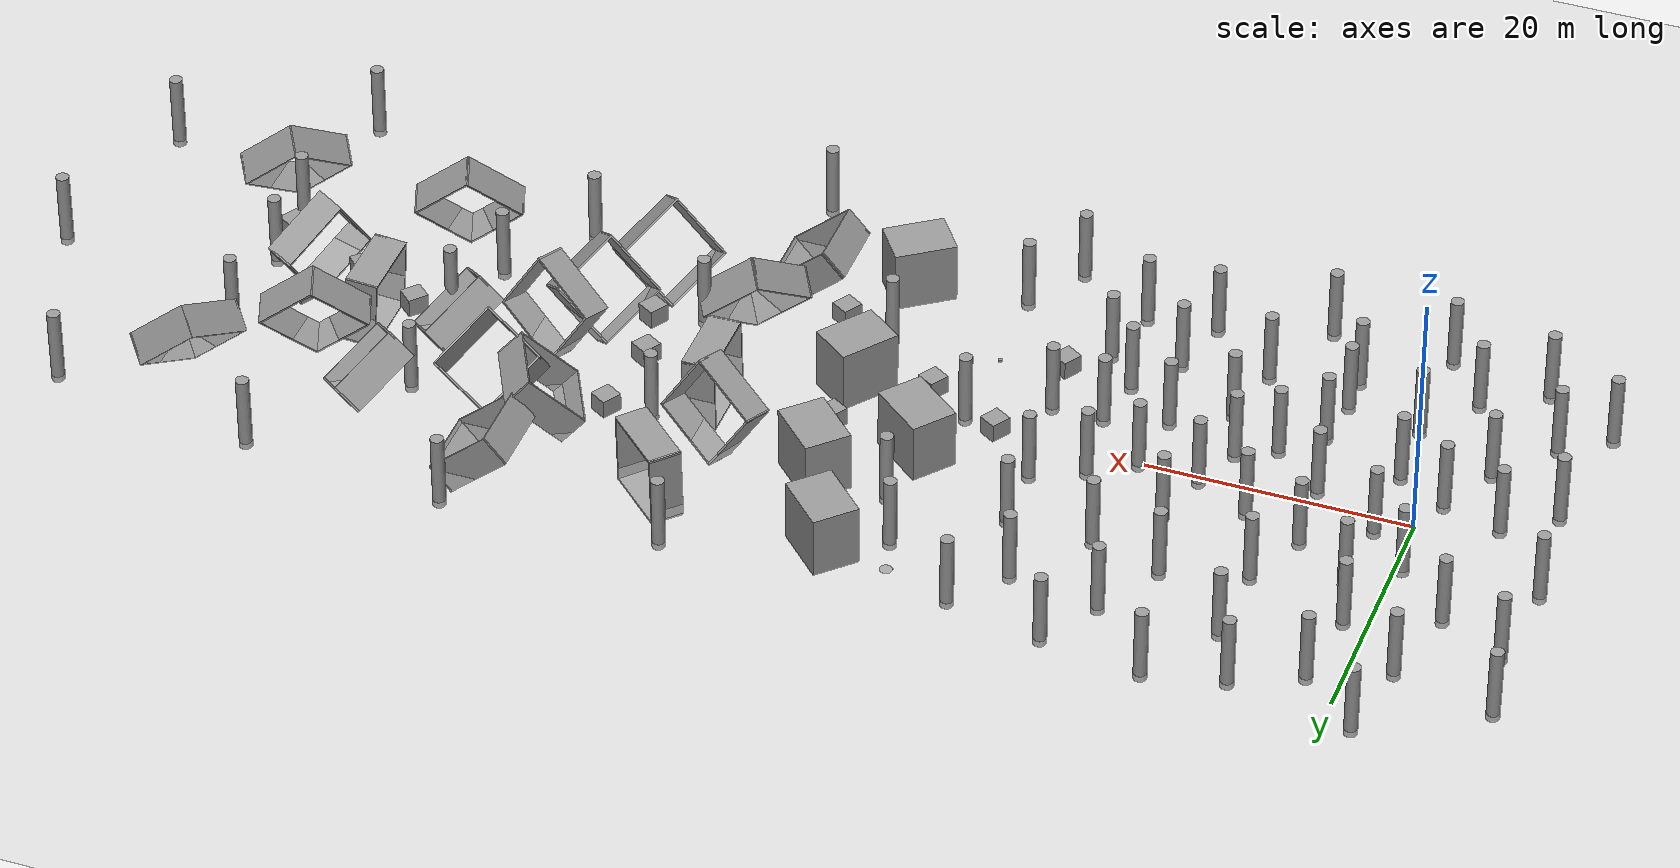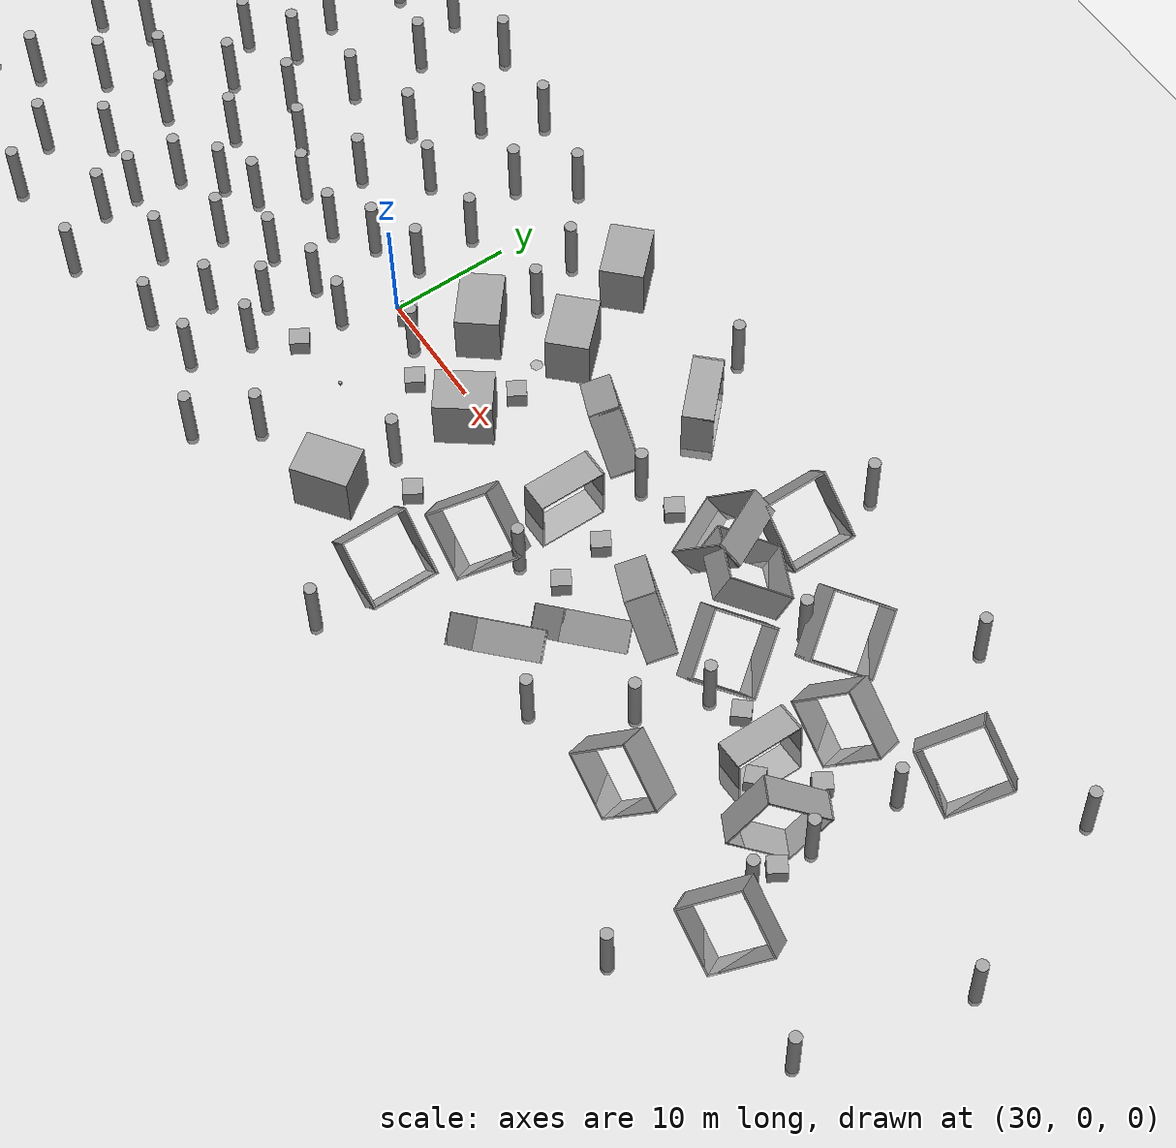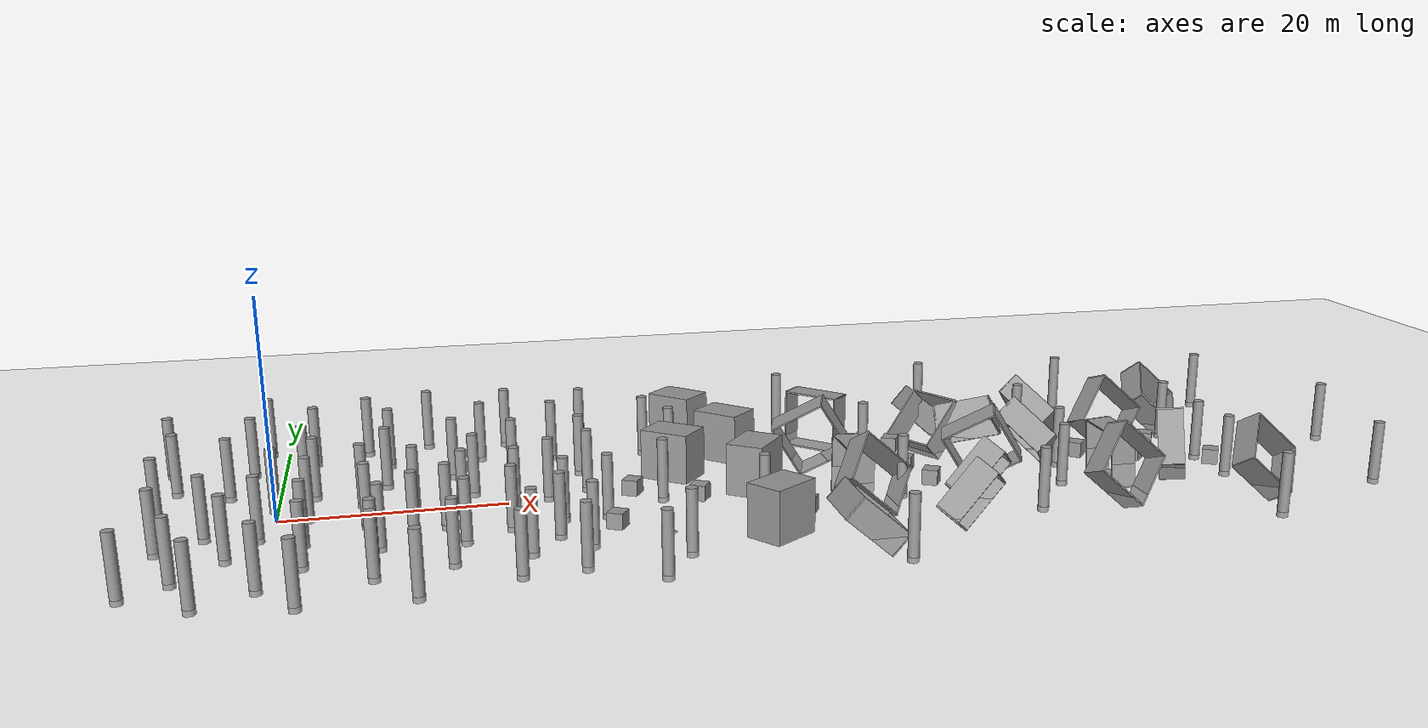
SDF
<sdf version="1.6">
 <world name="default">
  <plugin name="disable_physics" filename="libdisable_physics.so"/>
  <light name="sun" type="directional">
   <cast_shadows>0</cast_shadows>
   <pose>0 0 10 0 -0 0</pose>
   <diffuse>0.8 0.8 0.8 1</diffuse>
   <specular>0.2 0.2 0.2 1</specular>
   <attenuation>
    <range>1000</range>
    <constant>0.9</constant>
    <linear>0.01</linear>
    <quadratic>0.001</quadratic>
   </attenuation>
   <direction>-0.5 0.1 -0.9</direction>
  </light>
  <model name="ground_plane">
   <static>1</static>
   <link name="link">
    <collision name="collision">
     <geometry><plane><normal>0 0 1</normal><size>400 400</size></plane></geometry>
     <surface><friction><ode><mu>100</mu><mu2>50</mu2></ode></friction></surface>
    </collision>
    <visual name="visual">
     <cast_shadows>0</cast_shadows>
     <geometry><plane><normal>0 0 1</normal><size>200 200</size></plane></geometry>
     <material>
      <script><uri>file://media/materials/scripts/gazebo.material</uri><name>Gazebo/Grey</name></script>
     </material>
    </visual>
    <gravity>0</gravity>
   </link>
  </model>
  <physics name="default_physics" default="0" type="ode">
   <max_step_size>0.001</max_step_size>
   <real_time_factor>1</real_time_factor>
   <real_time_update_rate>1000</real_time_update_rate>
  </physics>
  <scene><ambient>0.4 0.4 0.4 1</ambient><background>0.7 0.7 0.7 1</background><shadows>0</shadows></scene>
  <spherical_coordinates>
   <surface_model>EARTH_WGS84</surface_model>
   <latitude_deg>0</latitude_deg>
   <longitude_deg>0</longitude_deg>
   <elevation>0</elevation>
   <heading_deg>0</heading_deg>
  </spherical_coordinates>
  <gravity>0 0 -9.8</gravity>
  <magnetic_field>6e-06 2.3e-05 -4.2e-05</magnetic_field>
  <atmosphere type="adiabatic"/>
  <model name="unit_cylinder_0">
   <static>1</static>
   <pose>36.5123 8.86063 -7.43476 0 -0 0</pose>
   <link name="link">
    <inertial>
     <mass>1</mass>
     <inertia><ixx>0.145833</ixx><ixy>0</ixy><ixz>0</ixz><iyy>0.145833</iyy><iyz>0</iyz><izz>0.125</izz></inertia>
    </inertial>
    <collision name="collision">
     <geometry><cylinder><radius>0.5</radius><length>0.000754659</length></cylinder></geometry>
     <surface><contact><collide_without_contact>1</collide_without_contact></contact></surface>
    </collision>
    <visual name="visual">
     <geometry><cylinder><radius>0.5</radius><length>0.000754659</length></cylinder></geometry>
     <material>
      <script><name>Gazebo/Grey</name><uri>file://media/materials/scripts/gazebo.material</uri></script>
     </material>
    </visual>
    <gravity>0</gravity>
   </link>
  </model>
  <model name="unit_cylinder_0_clone_14_clone_14">
   <static>1</static>
   <pose>26.2784 -11.4682 2.40172 0 -0 0.001073</pose>
   <link name="link">
    <inertial>
     <mass>1</mass>
     <inertia><ixx>0.145833</ixx><ixy>0</ixy><ixz>0</ixz><iyy>0.145833</iyy><iyz>0</iyz><izz>0.125</izz></inertia>
    </inertial>
    <collision name="collision">
     <geometry><cylinder><radius>0.5</radius><length>6.03342</length></cylinder></geometry>
     <surface><contact><collide_without_contact>1</collide_without_contact></contact></surface>
    </collision>
    <visual name="visual">
     <geometry><cylinder><radius>0.5</radius><length>6.03342</length></cylinder></geometry>
     <material>
      <script><name>Gazebo/Grey</name><uri>file://media/materials/scripts/gazebo.material</uri></script>
     </material>
    </visual>
    <gravity>0</gravity>
   </link>
  </model>
  <model name="unit_cylinder_0_clone_14_clone_9_clone">
   <static>1</static>
   <pose>27.6139 3.55096 2.40172 0 -0 0.001073</pose>
   <link name="link">
    <inertial>
     <mass>1</mass>
     <inertia><ixx>0.145833</ixx><ixy>0</ixy><ixz>0</ixz><iyy>0.145833</iyy><iyz>0</iyz><izz>0.125</izz></inertia>
    </inertial>
    <collision name="collision">
     <geometry><cylinder><radius>0.5</radius><length>6.03342</length></cylinder></geometry>
     <surface><contact><collide_without_contact>1</collide_without_contact></contact></surface>
    </collision>
    <visual name="visual">
     <geometry><cylinder><radius>0.5</radius><length>6.03342</length></cylinder></geometry>
     <material>
      <script><name>Gazebo/Grey</name><uri>file://media/materials/scripts/gazebo.material</uri></script>
     </material>
    </visual>
    <gravity>0</gravity>
   </link>
  </model>
  <model name="unit_cylinder_0_clone_14_clone_9_clone_0">
   <static>1</static>
   <pose>28.4771 -4.34225 2.40172 0 -0 0.001073</pose>
   <link name="link">
    <inertial>
     <mass>1</mass>
     <inertia><ixx>0.145833</ixx><ixy>0</ixy><ixz>0</ixz><iyy>0.145833</iyy><iyz>0</iyz><izz>0.125</izz></inertia>
    </inertial>
    <collision name="collision">
     <geometry><cylinder><radius>0.5</radius><length>6.03342</length></cylinder></geometry>
     <surface><contact><collide_without_contact>1</collide_without_contact></contact></surface>
    </collision>
    <visual name="visual">
     <geometry><cylinder><radius>0.5</radius><length>6.03342</length></cylinder></geometry>
     <material>
      <script><name>Gazebo/Grey</name><uri>file://media/materials/scripts/gazebo.material</uri></script>
     </material>
    </visual>
    <gravity>0</gravity>
   </link>
  </model>
  <model name="unit_cylinder_0_clone_14_clone_9_clone_1">
   <static>1</static>
   <pose>24.5651 -4.32645 2.40172 0 -0 0.001073</pose>
   <link name="link">
    <inertial>
     <mass>1</mass>
     <inertia><ixx>0.145833</ixx><ixy>0</ixy><ixz>0</ixz><iyy>0.145833</iyy><iyz>0</iyz><izz>0.125</izz></inertia>
    </inertial>
    <collision name="collision">
     <geometry><cylinder><radius>0.5</radius><length>6.03342</length></cylinder></geometry>
     <surface><contact><collide_without_contact>1</collide_without_contact></contact></surface>
    </collision>
    <visual name="visual">
     <geometry><cylinder><radius>0.5</radius><length>6.03342</length></cylinder></geometry>
     <material>
      <script><name>Gazebo/Grey</name><uri>file://media/materials/scripts/gazebo.material</uri></script>
     </material>
    </visual>
    <gravity>0</gravity>
   </link>
  </model>
  <model name="unit_cylinder_0_clone_14_clone_9_clone_5">
   <static>1</static>
   <pose>23.8422 1.77062 2.40172 0 -0 0.001073</pose>
   <link name="link">
    <inertial>
     <mass>1</mass>
     <inertia><ixx>0.145833</ixx><ixy>0</ixy><ixz>0</ixz><iyy>0.145833</iyy><iyz>0</iyz><izz>0.125</izz></inertia>
    </inertial>
    <collision name="collision">
     <geometry><cylinder><radius>0.5</radius><length>6.03342</length></cylinder></geometry>
     <surface><contact><collide_without_contact>1</collide_without_contact></contact></surface>
    </collision>
    <visual name="visual">
     <geometry><cylinder><radius>0.5</radius><length>6.03342</length></cylinder></geometry>
     <material>
      <script><name>Gazebo/Grey</name><uri>file://media/materials/scripts/gazebo.material</uri></script>
     </material>
    </visual>
    <gravity>0</gravity>
   </link>
  </model>
  <model name="unit_cylinder_0_clone_14_clone_9_clone_6_clone">
   <static>1</static>
   <pose>17.2344 4.59319 2.40172 0 -0 0.001073</pose>
   <link name="link">
    <inertial>
     <mass>1</mass>
     <inertia><ixx>0.145833</ixx><ixy>0</ixy><ixz>0</ixz><iyy>0.145833</iyy><iyz>0</iyz><izz>0.125</izz></inertia>
    </inertial>
    <collision name="collision">
     <geometry><cylinder><radius>0.5</radius><length>6.03342</length></cylinder></geometry>
     <surface><contact><collide_without_contact>1</collide_without_contact></contact></surface>
    </collision>
    <visual name="visual">
     <geometry><cylinder><radius>0.5</radius><length>6.03342</length></cylinder></geometry>
     <material>
      <script><name>Gazebo/Grey</name><uri>file://media/materials/scripts/gazebo.material</uri></script>
     </material>
    </visual>
    <gravity>0</gravity>
   </link>
  </model>
  <model name="unit_cylinder_0_clone_14_clone_9_clone_6_clone_0">
   <static>1</static>
   <pose>16 0 2.40172 0 -0 0.001073</pose>
   <link name="link">
    <inertial>
     <mass>1</mass>
     <inertia><ixx>0.145833</ixx><ixy>0</ixy><ixz>0</ixz><iyy>0.145833</iyy><iyz>0</iyz><izz>0.125</izz></inertia>
    </inertial>
    <collision name="collision">
     <geometry><cylinder><radius>0.5</radius><length>6.03342</length></cylinder></geometry>
     <surface><contact><collide_without_contact>1</collide_without_contact></contact></surface>
    </collision>
    <visual name="visual">
     <geometry><cylinder><radius>0.5</radius><length>6.03342</length></cylinder></geometry>
     <material>
      <script><name>Gazebo/Grey</name><uri>file://media/materials/scripts/gazebo.material</uri></script>
     </material>
    </visual>
    <gravity>0</gravity>
   </link>
  </model>
  <model name="unit_cylinder_0_clone_14_clone_9_clone_6_clone_1">
   <static>1</static>
   <pose>15.9275 -8.02091 2.40172 0 -0 0.001073</pose>
   <link name="link">
    <inertial>
     <mass>1</mass>
     <inertia><ixx>0.145833</ixx><ixy>0</ixy><ixz>0</ixz><iyy>0.145833</iyy><iyz>0</iyz><izz>0.125</izz></inertia>
    </inertial>
    <collision name="collision">
     <geometry><cylinder><radius>0.5</radius><length>6.03342</length></cylinder></geometry>
     <surface><contact><collide_without_contact>1</collide_without_contact></contact></surface>
    </collision>
    <visual name="visual">
     <geometry><cylinder><radius>0.5</radius><length>6.03342</length></cylinder></geometry>
     <material>
      <script><name>Gazebo/Grey</name><uri>file://media/materials/scripts/gazebo.material</uri></script>
     </material>
    </visual>
    <gravity>0</gravity>
   </link>
  </model>
  <model name="unit_cylinder_0_clone_14_clone_9_clone_6_clone_3">
   <static>1</static>
   <pose>15.5728 10.4838 2.40172 0 -0 0.001073</pose>
   <link name="link">
    <inertial>
     <mass>1</mass>
     <inertia><ixx>0.145833</ixx><ixy>0</ixy><ixz>0</ixz><iyy>0.145833</iyy><iyz>0</iyz><izz>0.125</izz></inertia>
    </inertial>
    <collision name="collision">
     <geometry><cylinder><radius>0.5</radius><length>6.03342</length></cylinder></geometry>
     <surface><contact><collide_without_contact>1</collide_without_contact></contact></surface>
    </collision>
    <visual name="visual">
     <geometry><cylinder><radius>0.5</radius><length>6.03342</length></cylinder></geometry>
     <material>
      <script><name>Gazebo/Grey</name><uri>file://media/materials/scripts/gazebo.material</uri></script>
     </material>
    </visual>
    <gravity>0</gravity>
   </link>
  </model>
  <model name="unit_cylinder_0_clone_14_clone_9_clone_6_clone_7">
   <static>1</static>
   <pose>20.62 -0.359864 2.40172 0 -0 0.001073</pose>
   <link name="link">
    <inertial>
     <mass>1</mass>
     <inertia><ixx>0.145833</ixx><ixy>0</ixy><ixz>0</ixz><iyy>0.145833</iyy><iyz>0</iyz><izz>0.125</izz></inertia>
    </inertial>
    <collision name="collision">
     <geometry><cylinder><radius>0.5</radius><length>6.03342</length></cylinder></geometry>
     <surface><contact><collide_without_contact>1</collide_without_contact></contact></surface>
    </collision>
    <visual name="visual">
     <geometry><cylinder><radius>0.5</radius><length>6.03342</length></cylinder></geometry>
     <material>
      <script><name>Gazebo/Grey</name><uri>file://media/materials/scripts/gazebo.material</uri></script>
     </material>
    </visual>
    <gravity>0</gravity>
   </link>
  </model>
  <model name="unit_cylinder_0_clone_14_clone_9_clone_6_clone_8">
   <static>1</static>
   <pose>14.4535 -3.71562 2.40172 0 -0 0.001073</pose>
   <link name="link">
    <inertial>
     <mass>1</mass>
     <inertia><ixx>0.145833</ixx><ixy>0</ixy><ixz>0</ixz><iyy>0.145833</iyy><iyz>0</iyz><izz>0.125</izz></inertia>
    </inertial>
    <collision name="collision">
     <geometry><cylinder><radius>0.5</radius><length>6.03342</length></cylinder></geometry>
     <surface><contact><collide_without_contact>1</collide_without_contact></contact></surface>
    </collision>
    <visual name="visual">
     <geometry><cylinder><radius>0.5</radius><length>6.03342</length></cylinder></geometry>
     <material>
      <script><name>Gazebo/Grey</name><uri>file://media/materials/scripts/gazebo.material</uri></script>
     </material>
    </visual>
    <gravity>0</gravity>
   </link>
  </model>
  <model name="unit_cylinder_0_clone_14_clone_9_clone_1_clone">
   <static>1</static>
   <pose>19.9723 -5.56562 2.40172 0 -0 0.001073</pose>
   <link name="link">
    <inertial>
     <mass>1</mass>
     <inertia><ixx>0.145833</ixx><ixy>0</ixy><ixz>0</ixz><iyy>0.145833</iyy><iyz>0</iyz><izz>0.125</izz></inertia>
    </inertial>
    <collision name="collision">
     <geometry><cylinder><radius>0.5</radius><length>6.03342</length></cylinder></geometry>
     <surface><contact><collide_without_contact>1</collide_without_contact></contact></surface>
    </collision>
    <visual name="visual">
     <geometry><cylinder><radius>0.5</radius><length>6.03342</length></cylinder></geometry>
     <material>
      <script><name>Gazebo/Grey</name><uri>file://media/materials/scripts/gazebo.material</uri></script>
     </material>
    </visual>
    <gravity>0</gravity>
   </link>
  </model>
  <model name="unit_cylinder_0_clone_14_clone_9_clone_1_clone_0">
   <static>1</static>
   <pose>23.821 -8.50291 2.40172 0 -0 0.001073</pose>
   <link name="link">
    <inertial>
     <mass>1</mass>
     <inertia><ixx>0.145833</ixx><ixy>0</ixy><ixz>0</ixz><iyy>0.145833</iyy><iyz>0</iyz><izz>0.125</izz></inertia>
    </inertial>
    <collision name="collision">
     <geometry><cylinder><radius>0.5</radius><length>6.03342</length></cylinder></geometry>
     <surface><contact><collide_without_contact>1</collide_without_contact></contact></surface>
    </collision>
    <visual name="visual">
     <geometry><cylinder><radius>0.5</radius><length>6.03342</length></cylinder></geometry>
     <material>
      <script><name>Gazebo/Grey</name><uri>file://media/materials/scripts/gazebo.material</uri></script>
     </material>
    </visual>
    <gravity>0</gravity>
   </link>
  </model>
  <model name="unit_cylinder_0_clone_14_clone_9_clone_1_clone_1">
   <static>1</static>
   <pose>21.0632 8.86959 2.40172 0 -0 0.001073</pose>
   <link name="link">
    <inertial>
     <mass>1</mass>
     <inertia><ixx>0.145833</ixx><ixy>0</ixy><ixz>0</ixz><iyy>0.145833</iyy><iyz>0</iyz><izz>0.125</izz></inertia>
    </inertial>
    <collision name="collision">
     <geometry><cylinder><radius>0.5</radius><length>6.03342</length></cylinder></geometry>
     <surface><contact><collide_without_contact>1</collide_without_contact></contact></surface>
    </collision>
    <visual name="visual">
     <geometry><cylinder><radius>0.5</radius><length>6.03342</length></cylinder></geometry>
     <material>
      <script><name>Gazebo/Grey</name><uri>file://media/materials/scripts/gazebo.material</uri></script>
     </material>
    </visual>
    <gravity>0</gravity>
   </link>
  </model>
  <model name="unit_cylinder_0_clone_14_clone_14_clone">
   <static>1</static>
   <pose>27.4778 8.76956 2.40172 0 -0 0.001073</pose>
   <link name="link">
    <inertial>
     <mass>1</mass>
     <inertia><ixx>0.145833</ixx><ixy>0</ixy><ixz>0</ixz><iyy>0.145833</iyy><iyz>0</iyz><izz>0.125</izz></inertia>
    </inertial>
    <collision name="collision">
     <geometry><cylinder><radius>0.5</radius><length>6.03342</length></cylinder></geometry>
     <surface><contact><collide_without_contact>1</collide_without_contact></contact></surface>
    </collision>
    <visual name="visual">
     <geometry><cylinder><radius>0.5</radius><length>6.03342</length></cylinder></geometry>
     <material>
      <script><name>Gazebo/Grey</name><uri>file://media/materials/scripts/gazebo.material</uri></script>
     </material>
    </visual>
    <gravity>0</gravity>
   </link>
  </model>
  <model name="unit_box_0">
   <pose>33.6091 -7.66217 0.102875 0 -0 0.311003</pose>
   <link name="link">
    <inertial>
     <mass>1</mass>
     <inertia>
      <ixx>0.166667</ixx>
      <ixy>0</ixy>
      <ixz>0</ixz>
      <iyy>0.166667</iyy>
      <iyz>0</iyz>
      <izz>0.166667</izz>
     </inertia>
    </inertial>
    <collision name="collision">
     <geometry><box><size>0.280027 0.211756 0.205751</size></box></geometry>
    </collision>
    <visual name="visual">
     <geometry><box><size>0.280027 0.211756 0.205751</size></box></geometry>
     <material>
      <script><name>Gazebo/Grey</name><uri>file://media/materials/scripts/gazebo.material</uri></script>
     </material>
    </visual>
   </link>
  </model>
  <model name="unit_box_0_clone">
   <pose>35.8595 4.28489 2.36118 1.5708 -1e-06 0.886453</pose>
   <link name="link">
    <inertial>
     <mass>1</mass>
     <inertia>
      <ixx>0.166667</ixx>
      <ixy>0</ixy>
      <ixz>0</ixz>
      <iyy>0.166667</iyy>
      <iyz>0</iyz>
      <izz>0.166667</izz>
     </inertia>
    </inertial>
    <collision name="collision"><geometry><box><size>3.57109 4.72237 4.86028</size></box></geometry></collision>
    <visual name="visual">
     <geometry><box><size>3.57109 4.72237 4.86028</size></box></geometry>
     <material>
      <script><name>Gazebo/Grey</name><uri>file://media/materials/scripts/gazebo.material</uri></script>
     </material>
    </visual>
   </link>
  </model>
  <model name="unit_box_0_clone_0">
   <pose>42.4872 -1.52104 2.43013 1e-06 -0 -0.648959</pose>
   <link name="link">
    <inertial>
     <mass>1</mass>
     <inertia>
      <ixx>0.166667</ixx>
      <ixy>0</ixy>
      <ixz>0</ixz>
      <iyy>0.166667</iyy>
      <iyz>0</iyz>
      <izz>0.166667</izz>
     </inertia>
    </inertial>
    <collision name="collision"><geometry><box><size>3.57109 4.72237 4.86028</size></box></geometry></collision>
    <visual name="visual">
     <geometry><box><size>3.57109 4.72237 4.86028</size></box></geometry>
     <material>
      <script><name>Gazebo/Grey</name><uri>file://media/materials/scripts/gazebo.material</uri></script>
     </material>
    </visual>
   </link>
  </model>
  <model name="unit_box_0_clone_1">
   <pose>41.9571 -13.6235 2.43014 -1e-06 -0 -0.952393</pose>
   <link name="link">
    <inertial>
     <mass>1</mass>
     <inertia>
      <ixx>0.166667</ixx>
      <ixy>0</ixy>
      <ixz>0</ixz>
      <iyy>0.166667</iyy>
      <iyz>0</iyz>
      <izz>0.166667</izz>
     </inertia>
    </inertial>
    <collision name="collision"><geometry><box><size>3.57109 4.72237 4.86028</size></box></geometry></collision>
    <visual name="visual">
     <geometry><box><size>3.57109 4.72237 4.86028</size></box></geometry>
     <material>
      <script><name>Gazebo/Grey</name><uri>file://media/materials/scripts/gazebo.material</uri></script>
     </material>
    </visual>
   </link>
  </model>
  <model name="unit_box_0_clone_clone_clone">
   <pose>37.0789 -2.79874 0.73007 1.57079 -0 1.02322</pose>
   <link name="link">
    <inertial>
     <mass>1</mass>
     <inertia>
      <ixx>0.166667</ixx>
      <ixy>0</ixy>
      <ixz>0</ixz>
      <iyy>0.166667</iyy>
      <iyz>0</iyz>
      <izz>0.166667</izz>
     </inertia>
    </inertial>
    <collision name="collision"><geometry><box><size>1.57977 1.46015 1.47659</size></box></geometry></collision>
    <visual name="visual">
     <geometry><box><size>1.57977 1.46015 1.47659</size></box></geometry>
     <material>
      <script><name>Gazebo/Grey</name><uri>file://media/materials/scripts/gazebo.material</uri></script>
     </material>
    </visual>
   </link>
  </model>
  <model name="unit_box_0_clone_clone_clone_0">
   <pose>31.3347 0.144887 0.73007 1.57079 -0 1.02322</pose>
   <link name="link">
    <inertial>
     <mass>1</mass>
     <inertia>
      <ixx>0.166667</ixx>
      <ixy>0</ixy>
      <ixz>0</ixz>
      <iyy>0.166667</iyy>
      <iyz>0</iyz>
      <izz>0.166667</izz>
     </inertia>
    </inertial>
    <collision name="collision"><geometry><box><size>1.57977 1.46015 1.47659</size></box></geometry></collision>
    <visual name="visual">
     <geometry><box><size>1.57977 1.46015 1.47659</size></box></geometry>
     <material>
      <script><name>Gazebo/Grey</name><uri>file://media/materials/scripts/gazebo.material</uri></script>
     </material>
    </visual>
   </link>
  </model>
  <model name="unit_box_0_clone_clone_clone_1">
   <pose>28.7532 -8.3672 0.73007 1.57079 -0 1.02322</pose>
   <link name="link">
    <inertial>
     <mass>1</mass>
     <inertia>
      <ixx>0.166667</ixx>
      <ixy>0</ixy>
      <ixz>0</ixz>
      <iyy>0.166667</iyy>
      <iyz>0</iyz>
      <izz>0.166667</izz>
     </inertia>
    </inertial>
    <collision name="collision"><geometry><box><size>1.57977 1.46015 1.47659</size></box></geometry></collision>
    <visual name="visual">
     <geometry><box><size>1.57977 1.46015 1.47659</size></box></geometry>
     <material>
      <script><name>Gazebo/Grey</name><uri>file://media/materials/scripts/gazebo.material</uri></script>
     </material>
    </visual>
   </link>
  </model>
  <model name="unit_box_0_clone_clone_clone_2">
   <pose>42.7082 3.13136 0.73007 1.57079 -0 1.02322</pose>
   <link name="link">
    <inertial>
     <mass>1</mass>
     <inertia>
      <ixx>0.166667</ixx>
      <ixy>0</ixy>
      <ixz>0</ixz>
      <iyy>0.166667</iyy>
      <iyz>0</iyz>
      <izz>0.166667</izz>
     </inertia>
    </inertial>
    <collision name="collision"><geometry><box><size>1.57977 1.46015 1.47659</size></box></geometry></collision>
    <visual name="visual">
     <geometry><box><size>1.57977 1.46015 1.47659</size></box></geometry>
     <material>
      <script><name>Gazebo/Grey</name><uri>file://media/materials/scripts/gazebo.material</uri></script>
     </material>
    </visual>
   </link>
  </model>
  <model name="unit_box_0_clone_clone_clone_3">
   <pose>45.775 -8.54486 0.73007 1.57079 -0 1.02322</pose>
   <link name="link">
    <inertial>
     <mass>1</mass>
     <inertia>
      <ixx>0.166667</ixx>
      <ixy>0</ixy>
      <ixz>0</ixz>
      <iyy>0.166667</iyy>
      <iyz>0</iyz>
      <izz>0.166667</izz>
     </inertia>
    </inertial>
    <collision name="collision"><geometry><box><size>1.57977 1.46015 1.47659</size></box></geometry></collision>
    <visual name="visual">
     <geometry><box><size>1.57977 1.46015 1.47659</size></box></geometry>
     <material>
      <script><name>Gazebo/Grey</name><uri>file://media/materials/scripts/gazebo.material</uri></script>
     </material>
    </visual>
   </link>
  </model>
  <model name="unit_cylinder_0_clone_14_clone_9_clone_6_clone_3_clone">
   <static>1</static>
   <pose>9.40132 8.7634 2.40172 0 -0 0.001073</pose>
   <link name="link">
    <inertial>
     <mass>1</mass>
     <inertia><ixx>0.145833</ixx><ixy>0</ixy><ixz>0</ixz><iyy>0.145833</iyy><iyz>0</iyz><izz>0.125</izz></inertia>
    </inertial>
    <collision name="collision">
     <geometry><cylinder><radius>0.5</radius><length>6.03342</length></cylinder></geometry>
     <surface><contact><collide_without_contact>1</collide_without_contact></contact></surface>
    </collision>
    <visual name="visual">
     <geometry><cylinder><radius>0.5</radius><length>6.03342</length></cylinder></geometry>
     <material>
      <script><name>Gazebo/Grey</name><uri>file://media/materials/scripts/gazebo.material</uri></script>
     </material>
    </visual>
    <gravity>0</gravity>
   </link>
  </model>
  <model name="unit_cylinder_0_clone_14_clone_9_clone_6_clone_3_clone_0">
   <static>1</static>
   <pose>7.25639 3.9523 2.40172 0 -0 0.001073</pose>
   <link name="link">
    <inertial>
     <mass>1</mass>
     <inertia><ixx>0.145833</ixx><ixy>0</ixy><ixz>0</ixz><iyy>0.145833</iyy><iyz>0</iyz><izz>0.125</izz></inertia>
    </inertial>
    <collision name="collision">
     <geometry><cylinder><radius>0.5</radius><length>6.03342</length></cylinder></geometry>
     <surface><contact><collide_without_contact>1</collide_without_contact></contact></surface>
    </collision>
    <visual name="visual">
     <geometry><cylinder><radius>0.5</radius><length>6.03342</length></cylinder></geometry>
     <material>
      <script><name>Gazebo/Grey</name><uri>file://media/materials/scripts/gazebo.material</uri></script>
     </material>
    </visual>
    <gravity>0</gravity>
   </link>
  </model>
  <model name="unit_cylinder_0_clone_14_clone_9_clone_6_clone_3_clone_1">
   <static>1</static>
   <pose>7.67753 -1.86181 2.40172 0 -0 0.001073</pose>
   <link name="link">
    <inertial>
     <mass>1</mass>
     <inertia><ixx>0.145833</ixx><ixy>0</ixy><ixz>0</ixz><iyy>0.145833</iyy><iyz>0</iyz><izz>0.125</izz></inertia>
    </inertial>
    <collision name="collision">
     <geometry><cylinder><radius>0.5</radius><length>6.03342</length></cylinder></geometry>
     <surface><contact><collide_without_contact>1</collide_without_contact></contact></surface>
    </collision>
    <visual name="visual">
     <geometry><cylinder><radius>0.5</radius><length>6.03342</length></cylinder></geometry>
     <material>
      <script><name>Gazebo/Grey</name><uri>file://media/materials/scripts/gazebo.material</uri></script>
     </material>
    </visual>
    <gravity>0</gravity>
   </link>
  </model>
  <model name="unit_cylinder_0_clone_14_clone_9_clone_6_clone_3_clone_2">
   <static>1</static>
   <pose>3 7 2.40172 0 -0 0.001073</pose>
   <link name="link">
    <inertial>
     <mass>1</mass>
     <inertia><ixx>0.145833</ixx><ixy>0</ixy><ixz>0</ixz><iyy>0.145833</iyy><iyz>0</iyz><izz>0.125</izz></inertia>
    </inertial>
    <collision name="collision">
     <geometry><cylinder><radius>0.5</radius><length>6.03342</length></cylinder></geometry>
     <surface><contact><collide_without_contact>1</collide_without_contact></contact></surface>
    </collision>
    <visual name="visual">
     <geometry><cylinder><radius>0.5</radius><length>6.03342</length></cylinder></geometry>
     <material>
      <script><name>Gazebo/Grey</name><uri>file://media/materials/scripts/gazebo.material</uri></script>
     </material>
    </visual>
    <gravity>0</gravity>
   </link>
  </model>
  <model name="unit_cylinder_0_clone_14_clone_9_clone_6_clone_3_clone_3">
   <static>1</static>
   <pose>2.62841 0.991234 2.40172 0 -0 0.001073</pose>
   <link name="link">
    <inertial>
     <mass>1</mass>
     <inertia><ixx>0.145833</ixx><ixy>0</ixy><ixz>0</ixz><iyy>0.145833</iyy><iyz>0</iyz><izz>0.125</izz></inertia>
    </inertial>
    <collision name="collision">
     <geometry><cylinder><radius>0.5</radius><length>6.03342</length></cylinder></geometry>
     <surface><contact><collide_without_contact>1</collide_without_contact></contact></surface>
    </collision>
    <visual name="visual">
     <geometry><cylinder><radius>0.5</radius><length>6.03342</length></cylinder></geometry>
     <material>
      <script><name>Gazebo/Grey</name><uri>file://media/materials/scripts/gazebo.material</uri></script>
     </material>
    </visual>
    <gravity>0</gravity>
   </link>
  </model>
  <model name="unit_cylinder_0_clone_14_clone_9_clone_6_clone_3_clone_4">
   <static>1</static>
   <pose>2.51783 -5.37737 2.40172 0 -0 0.001073</pose>
   <link name="link">
    <inertial>
     <mass>1</mass>
     <inertia><ixx>0.145833</ixx><ixy>0</ixy><ixz>0</ixz><iyy>0.145833</iyy><iyz>0</iyz><izz>0.125</izz></inertia>
    </inertial>
    <collision name="collision">
     <geometry><cylinder><radius>0.5</radius><length>6.03342</length></cylinder></geometry>
     <surface><contact><collide_without_contact>1</collide_without_contact></contact></surface>
    </collision>
    <visual name="visual">
     <geometry><cylinder><radius>0.5</radius><length>6.03342</length></cylinder></geometry>
     <material>
      <script><name>Gazebo/Grey</name><uri>file://media/materials/scripts/gazebo.material</uri></script>
     </material>
    </visual>
    <gravity>0</gravity>
   </link>
  </model>
  <model name="unit_cylinder_0_clone_14_clone_9_clone_6_clone_3_clone_5">
   <static>1</static>
   <pose>8.83799 -7.80804 2.40172 0 -0 0.001073</pose>
   <link name="link">
    <inertial>
     <mass>1</mass>
     <inertia><ixx>0.145833</ixx><ixy>0</ixy><ixz>0</ixz><iyy>0.145833</iyy><iyz>0</iyz><izz>0.125</izz></inertia>
    </inertial>
    <collision name="collision">
     <geometry><cylinder><radius>0.5</radius><length>6.03342</length></cylinder></geometry>
     <surface><contact><collide_without_contact>1</collide_without_contact></contact></surface>
    </collision>
    <visual name="visual">
     <geometry><cylinder><radius>0.5</radius><length>6.03342</length></cylinder></geometry>
     <material>
      <script><name>Gazebo/Grey</name><uri>file://media/materials/scripts/gazebo.material</uri></script>
     </material>
    </visual>
    <gravity>0</gravity>
   </link>
  </model>
  <model name="unit_cylinder_0_clone_14_clone_9_clone_6_clone_3_clone_6">
   <static>1</static>
   <pose>-0.445316 4.32118 2.40172 0 -0 0.001073</pose>
   <link name="link">
    <inertial>
     <mass>1</mass>
     <inertia><ixx>0.145833</ixx><ixy>0</ixy><ixz>0</ixz><iyy>0.145833</iyy><iyz>0</iyz><izz>0.125</izz></inertia>
    </inertial>
    <collision name="collision">
     <geometry><cylinder><radius>0.5</radius><length>6.03342</length></cylinder></geometry>
     <surface><contact><collide_without_contact>1</collide_without_contact></contact></surface>
    </collision>
    <visual name="visual">
     <geometry><cylinder><radius>0.5</radius><length>6.03342</length></cylinder></geometry>
     <material>
      <script><name>Gazebo/Grey</name><uri>file://media/materials/scripts/gazebo.material</uri></script>
     </material>
    </visual>
    <gravity>0</gravity>
   </link>
  </model>
  <model name="unit_cylinder_0_clone_14_clone_9_clone_6_clone_3_clone_7">
   <static>1</static>
   <pose>-1.26097 -3.357 2.40172 0 -0 0.001073</pose>
   <link name="link">
    <inertial>
     <mass>1</mass>
     <inertia><ixx>0.145833</ixx><ixy>0</ixy><ixz>0</ixz><iyy>0.145833</iyy><iyz>0</iyz><izz>0.125</izz></inertia>
    </inertial>
    <collision name="collision">
     <geometry><cylinder><radius>0.5</radius><length>6.03342</length></cylinder></geometry>
     <surface><contact><collide_without_contact>1</collide_without_contact></contact></surface>
    </collision>
    <visual name="visual">
     <geometry><cylinder><radius>0.5</radius><length>6.03342</length></cylinder></geometry>
     <material>
      <script><name>Gazebo/Grey</name><uri>file://media/materials/scripts/gazebo.material</uri></script>
     </material>
    </visual>
    <gravity>0</gravity>
   </link>
  </model>
  <model name="unit_cylinder_0_clone_14_clone_9_clone_6_clone_3_clone_9">
   <static>1</static>
   <pose>-3.53682 -7.78165 2.40172 0 -0 0.001073</pose>
   <link name="link">
    <inertial>
     <mass>1</mass>
     <inertia><ixx>0.145833</ixx><ixy>0</ixy><ixz>0</ixz><iyy>0.145833</iyy><iyz>0</iyz><izz>0.125</izz></inertia>
    </inertial>
    <collision name="collision">
     <geometry><cylinder><radius>0.5</radius><length>6.03342</length></cylinder></geometry>
     <surface><contact><collide_without_contact>1</collide_without_contact></contact></surface>
    </collision>
    <visual name="visual">
     <geometry><cylinder><radius>0.5</radius><length>6.03342</length></cylinder></geometry>
     <material>
      <script><name>Gazebo/Grey</name><uri>file://media/materials/scripts/gazebo.material</uri></script>
     </material>
    </visual>
    <gravity>0</gravity>
   </link>
  </model>
  <model name="unit_cylinder_0_clone_14_clone_9_clone_6_clone_3_clone_10">
   <static>1</static>
   <pose>2.69205 -10.772 2.40172 0 -0 0.001073</pose>
   <link name="link">
    <inertial>
     <mass>1</mass>
     <inertia><ixx>0.145833</ixx><ixy>0</ixy><ixz>0</ixz><iyy>0.145833</iyy><iyz>0</iyz><izz>0.125</izz></inertia>
    </inertial>
    <collision name="collision">
     <geometry><cylinder><radius>0.5</radius><length>6.03342</length></cylinder></geometry>
     <surface><contact><collide_without_contact>1</collide_without_contact></contact></surface>
    </collision>
    <visual name="visual">
     <geometry><cylinder><radius>0.5</radius><length>6.03342</length></cylinder></geometry>
     <material>
      <script><name>Gazebo/Grey</name><uri>file://media/materials/scripts/gazebo.material</uri></script>
     </material>
    </visual>
    <gravity>0</gravity>
   </link>
  </model>
  <model name="unit_cylinder_0_clone_14_clone_9_clone_6_clone_3_clone_11">
   <static>1</static>
   <pose>-4.63021 8.56976 2.40172 0 -0 0.001073</pose>
   <link name="link">
    <inertial>
     <mass>1</mass>
     <inertia><ixx>0.145833</ixx><ixy>0</ixy><ixz>0</ixz><iyy>0.145833</iyy><iyz>0</iyz><izz>0.125</izz></inertia>
    </inertial>
    <collision name="collision">
     <geometry><cylinder><radius>0.5</radius><length>6.03342</length></cylinder></geometry>
     <surface><contact><collide_without_contact>1</collide_without_contact></contact></surface>
    </collision>
    <visual name="visual">
     <geometry><cylinder><radius>0.5</radius><length>6.03342</length></cylinder></geometry>
     <material>
      <script><name>Gazebo/Grey</name><uri>file://media/materials/scripts/gazebo.material</uri></script>
     </material>
    </visual>
    <gravity>0</gravity>
   </link>
  </model>
  <model name="unit_cylinder_0_clone_14_clone_9_clone_6_clone_3_clone_12">
   <static>1</static>
   <pose>1.83441 11.1369 2.40172 0 -0 0.001073</pose>
   <link name="link">
    <inertial>
     <mass>1</mass>
     <inertia><ixx>0.145833</ixx><ixy>0</ixy><ixz>0</ixz><iyy>0.145833</iyy><iyz>0</iyz><izz>0.125</izz></inertia>
    </inertial>
    <collision name="collision">
     <geometry><cylinder><radius>0.5</radius><length>6.03342</length></cylinder></geometry>
     <surface><contact><collide_without_contact>1</collide_without_contact></contact></surface>
    </collision>
    <visual name="visual">
     <geometry><cylinder><radius>0.5</radius><length>6.03342</length></cylinder></geometry>
     <material>
      <script><name>Gazebo/Grey</name><uri>file://media/materials/scripts/gazebo.material</uri></script>
     </material>
    </visual>
    <gravity>0</gravity>
   </link>
  </model>
  <model name="unit_cylinder_0_clone_14_clone_9_clone_6_clone_3_clone_13">
   <static>1</static>
   <pose>14.7274 -13.0156 2.40172 0 -0 0.001073</pose>
   <link name="link">
    <inertial>
     <mass>1</mass>
     <inertia><ixx>0.145833</ixx><ixy>0</ixy><ixz>0</ixz><iyy>0.145833</iyy><iyz>0</iyz><izz>0.125</izz></inertia>
    </inertial>
    <collision name="collision">
     <geometry><cylinder><radius>0.5</radius><length>6.03342</length></cylinder></geometry>
     <surface><contact><collide_without_contact>1</collide_without_contact></contact></surface>
    </collision>
    <visual name="visual">
     <geometry><cylinder><radius>0.5</radius><length>6.03342</length></cylinder></geometry>
     <material>
      <script><name>Gazebo/Grey</name><uri>file://media/materials/scripts/gazebo.material</uri></script>
     </material>
    </visual>
    <gravity>0</gravity>
   </link>
  </model>
  <model name="unit_cylinder_0_clone_14_clone_9_clone_6_clone_3_clone_14">
   <static>1</static>
   <pose>25.3694 14.4037 2.40172 0 -0 0.001073</pose>
   <link name="link">
    <inertial>
     <mass>1</mass>
     <inertia><ixx>0.145833</ixx><ixy>0</ixy><ixz>0</ixz><iyy>0.145833</iyy><iyz>0</iyz><izz>0.125</izz></inertia>
    </inertial>
    <collision name="collision">
     <geometry><cylinder><radius>0.5</radius><length>6.03342</length></cylinder></geometry>
     <surface><contact><collide_without_contact>1</collide_without_contact></contact></surface>
    </collision>
    <visual name="visual">
     <geometry><cylinder><radius>0.5</radius><length>6.03342</length></cylinder></geometry>
     <material>
      <script><name>Gazebo/Grey</name><uri>file://media/materials/scripts/gazebo.material</uri></script>
     </material>
    </visual>
    <gravity>0</gravity>
   </link>
  </model>
  <model name="unit_cylinder_0_clone_14_clone_9_clone_6_clone_3_clone_15">
   <static>1</static>
   <pose>-9.41044 -4.85539 2.40172 0 -0 0.001073</pose>
   <link name="link">
    <inertial>
     <mass>1</mass>
     <inertia><ixx>0.145833</ixx><ixy>0</ixy><ixz>0</ixz><iyy>0.145833</iyy><iyz>0</iyz><izz>0.125</izz></inertia>
    </inertial>
    <collision name="collision">
     <geometry><cylinder><radius>0.5</radius><length>6.03342</length></cylinder></geometry>
     <surface><contact><collide_without_contact>1</collide_without_contact></contact></surface>
    </collision>
    <visual name="visual">
     <geometry><cylinder><radius>0.5</radius><length>6.03342</length></cylinder></geometry>
     <material>
      <script><name>Gazebo/Grey</name><uri>file://media/materials/scripts/gazebo.material</uri></script>
     </material>
    </visual>
    <gravity>0</gravity>
   </link>
  </model>
  <model name="unit_cylinder_0_clone_14_clone_9_clone_6_clone_3_clone_16">
   <static>1</static>
   <pose>-10.3509 3.82373 2.40172 0 -0 0.001073</pose>
   <link name="link">
    <inertial>
     <mass>1</mass>
     <inertia><ixx>0.145833</ixx><ixy>0</ixy><ixz>0</ixz><iyy>0.145833</iyy><iyz>0</iyz><izz>0.125</izz></inertia>
    </inertial>
    <collision name="collision">
     <geometry><cylinder><radius>0.5</radius><length>6.03342</length></cylinder></geometry>
     <surface><contact><collide_without_contact>1</collide_without_contact></contact></surface>
    </collision>
    <visual name="visual">
     <geometry><cylinder><radius>0.5</radius><length>6.03342</length></cylinder></geometry>
     <material>
      <script><name>Gazebo/Grey</name><uri>file://media/materials/scripts/gazebo.material</uri></script>
     </material>
    </visual>
    <gravity>0</gravity>
   </link>
  </model>
  <model name="unit_cylinder_0_clone_14_clone_9_clone_6_clone_3_clone_8">
   <static>1</static>
   <pose>11.796 2.16375 2.40172 0 -0 0.001073</pose>
   <link name="link">
    <inertial>
     <mass>1</mass>
     <inertia><ixx>0.145833</ixx><ixy>0</ixy><ixz>0</ixz><iyy>0.145833</iyy><iyz>0</iyz><izz>0.125</izz></inertia>
    </inertial>
    <collision name="collision">
     <geometry><cylinder><radius>0.5</radius><length>6.03342</length></cylinder></geometry>
     <surface><contact><collide_without_contact>1</collide_without_contact></contact></surface>
    </collision>
    <visual name="visual">
     <geometry><cylinder><radius>0.5</radius><length>6.03342</length></cylinder></geometry>
     <material>
      <script><name>Gazebo/Grey</name><uri>file://media/materials/scripts/gazebo.material</uri></script>
     </material>
    </visual>
    <gravity>0</gravity>
   </link>
  </model>
  <model name="unit_cylinder_0_clone_14_clone_9_clone_6_clone_3_clone_17">
   <static>1</static>
   <pose>8.37013 -14.658 2.40172 0 -0 0.001073</pose>
   <link name="link">
    <inertial>
     <mass>1</mass>
     <inertia><ixx>0.145833</ixx><ixy>0</ixy><ixz>0</ixz><iyy>0.145833</iyy><iyz>0</iyz><izz>0.125</izz></inertia>
    </inertial>
    <collision name="collision">
     <geometry><cylinder><radius>0.5</radius><length>6.03342</length></cylinder></geometry>
     <surface><contact><collide_without_contact>1</collide_without_contact></contact></surface>
    </collision>
    <visual name="visual">
     <geometry><cylinder><radius>0.5</radius><length>6.03342</length></cylinder></geometry>
     <material>
      <script><name>Gazebo/Grey</name><uri>file://media/materials/scripts/gazebo.material</uri></script>
     </material>
    </visual>
    <gravity>0</gravity>
   </link>
  </model>
  <model name="unit_cylinder_0_clone_14_clone_9_clone_6_clone_3_clone_18">
   <static>1</static>
   <pose>9.67151 15.2058 2.40172 0 -0 0.001073</pose>
   <link name="link">
    <inertial>
     <mass>1</mass>
     <inertia><ixx>0.145833</ixx><ixy>0</ixy><ixz>0</ixz><iyy>0.145833</iyy><iyz>0</iyz><izz>0.125</izz></inertia>
    </inertial>
    <collision name="collision">
     <geometry><cylinder><radius>0.5</radius><length>6.03342</length></cylinder></geometry>
     <surface><contact><collide_without_contact>1</collide_without_contact></contact></surface>
    </collision>
    <visual name="visual">
     <geometry><cylinder><radius>0.5</radius><length>6.03342</length></cylinder></geometry>
     <material>
      <script><name>Gazebo/Grey</name><uri>file://media/materials/scripts/gazebo.material</uri></script>
     </material>
    </visual>
    <gravity>0</gravity>
   </link>
  </model>
  <model name="unit_cylinder_0_clone_14_clone_9_clone_6_clone_3_clone_18_clone">
   <static>1</static>
   <pose>18.4613 15.5209 2.40172 0 -0 0.001073</pose>
   <link name="link">
    <inertial>
     <mass>1</mass>
     <inertia><ixx>0.145833</ixx><ixy>0</ixy><ixz>0</ixz><iyy>0.145833</iyy><iyz>0</iyz><izz>0.125</izz></inertia>
    </inertial>
    <collision name="collision">
     <geometry><cylinder><radius>0.5</radius><length>6.03342</length></cylinder></geometry>
     <surface><contact><collide_without_contact>1</collide_without_contact></contact></surface>
    </collision>
    <visual name="visual">
     <geometry><cylinder><radius>0.5</radius><length>6.03342</length></cylinder></geometry>
     <material>
      <script><name>Gazebo/Grey</name><uri>file://media/materials/scripts/gazebo.material</uri></script>
     </material>
    </visual>
    <gravity>0</gravity>
   </link>
  </model>
  <model name="unit_cylinder_0_clone_14_clone_9_clone_6_clone_3_clone_18_clone_0">
   <static>1</static>
   <pose>2.58849 17.5445 2.40172 0 -0 0.001073</pose>
   <link name="link">
    <inertial>
     <mass>1</mass>
     <inertia><ixx>0.145833</ixx><ixy>0</ixy><ixz>0</ixz><iyy>0.145833</iyy><iyz>0</iyz><izz>0.125</izz></inertia>
    </inertial>
    <collision name="collision">
     <geometry><cylinder><radius>0.5</radius><length>6.03342</length></cylinder></geometry>
     <surface><contact><collide_without_contact>1</collide_without_contact></contact></surface>
    </collision>
    <visual name="visual">
     <geometry><cylinder><radius>0.5</radius><length>6.03342</length></cylinder></geometry>
     <material>
      <script><name>Gazebo/Grey</name><uri>file://media/materials/scripts/gazebo.material</uri></script>
     </material>
    </visual>
    <gravity>0</gravity>
   </link>
  </model>
  <model name="unit_cylinder_0_clone_14_clone_9_clone_6_clone_3_clone_18_clone_1">
   <static>1</static>
   <pose>-3.02406 15.1252 2.40172 0 -0 0.001073</pose>
   <link name="link">
    <inertial>
     <mass>1</mass>
     <inertia><ixx>0.145833</ixx><ixy>0</ixy><ixz>0</ixz><iyy>0.145833</iyy><iyz>0</iyz><izz>0.125</izz></inertia>
    </inertial>
    <collision name="collision">
     <geometry><cylinder><radius>0.5</radius><length>6.03342</length></cylinder></geometry>
     <surface><contact><collide_without_contact>1</collide_without_contact></contact></surface>
    </collision>
    <visual name="visual">
     <geometry><cylinder><radius>0.5</radius><length>6.03342</length></cylinder></geometry>
     <material>
      <script><name>Gazebo/Grey</name><uri>file://media/materials/scripts/gazebo.material</uri></script>
     </material>
    </visual>
    <gravity>0</gravity>
   </link>
  </model>
  <model name="unit_cylinder_0_clone_14_clone_9_clone_6_clone_3_clone_18_clone_2">
   <static>1</static>
   <pose>-10.6607 16.8177 2.40172 0 -0 0.001073</pose>
   <link name="link">
    <inertial>
     <mass>1</mass>
     <inertia><ixx>0.145833</ixx><ixy>0</ixy><ixz>0</ixz><iyy>0.145833</iyy><iyz>0</iyz><izz>0.125</izz></inertia>
    </inertial>
    <collision name="collision">
     <geometry><cylinder><radius>0.5</radius><length>6.03342</length></cylinder></geometry>
     <surface><contact><collide_without_contact>1</collide_without_contact></contact></surface>
    </collision>
    <visual name="visual">
     <geometry><cylinder><radius>0.5</radius><length>6.03342</length></cylinder></geometry>
     <material>
      <script><name>Gazebo/Grey</name><uri>file://media/materials/scripts/gazebo.material</uri></script>
     </material>
    </visual>
    <gravity>0</gravity>
   </link>
  </model>
  <model name="unit_cylinder_0_clone_14_clone_9_clone_6_clone_3_clone_18_clone_3">
   <static>1</static>
   <pose>-9.53338 11.0193 2.40172 0 -0 0.001073</pose>
   <link name="link">
    <inertial>
     <mass>1</mass>
     <inertia><ixx>0.145833</ixx><ixy>0</ixy><ixz>0</ixz><iyy>0.145833</iyy><iyz>0</iyz><izz>0.125</izz></inertia>
    </inertial>
    <collision name="collision">
     <geometry><cylinder><radius>0.5</radius><length>6.03342</length></cylinder></geometry>
     <surface><contact><collide_without_contact>1</collide_without_contact></contact></surface>
    </collision>
    <visual name="visual">
     <geometry><cylinder><radius>0.5</radius><length>6.03342</length></cylinder></geometry>
     <material>
      <script><name>Gazebo/Grey</name><uri>file://media/materials/scripts/gazebo.material</uri></script>
     </material>
    </visual>
    <gravity>0</gravity>
   </link>
  </model>
  <model name="unit_cylinder_0_clone_14_clone_9_clone_6_clone_3_clone_18_clone_4">
   <static>1</static>
   <pose>-5.77056 -2.129 2.40172 0 -0 0.001073</pose>
   <link name="link">
    <inertial>
     <mass>1</mass>
     <inertia><ixx>0.145833</ixx><ixy>0</ixy><ixz>0</ixz><iyy>0.145833</iyy><iyz>0</iyz><izz>0.125</izz></inertia>
    </inertial>
    <collision name="collision">
     <geometry><cylinder><radius>0.5</radius><length>6.03342</length></cylinder></geometry>
     <surface><contact><collide_without_contact>1</collide_without_contact></contact></surface>
    </collision>
    <visual name="visual">
     <geometry><cylinder><radius>0.5</radius><length>6.03342</length></cylinder></geometry>
     <material>
      <script><name>Gazebo/Grey</name><uri>file://media/materials/scripts/gazebo.material</uri></script>
     </material>
    </visual>
    <gravity>0</gravity>
   </link>
  </model>
  <model name="unit_cylinder_0_clone_14_clone_9_clone_6_clone_3_clone_18_clone_5">
   <static>1</static>
   <pose>-7.24573 -12.0876 2.40172 0 -0 0.001073</pose>
   <link name="link">
    <inertial>
     <mass>1</mass>
     <inertia><ixx>0.145833</ixx><ixy>0</ixy><ixz>0</ixz><iyy>0.145833</iyy><iyz>0</iyz><izz>0.125</izz></inertia>
    </inertial>
    <collision name="collision">
     <geometry><cylinder><radius>0.5</radius><length>6.03342</length></cylinder></geometry>
     <surface><contact><collide_without_contact>1</collide_without_contact></contact></surface>
    </collision>
    <visual name="visual">
     <geometry><cylinder><radius>0.5</radius><length>6.03342</length></cylinder></geometry>
     <material>
      <script><name>Gazebo/Grey</name><uri>file://media/materials/scripts/gazebo.material</uri></script>
     </material>
    </visual>
    <gravity>0</gravity>
   </link>
  </model>
  <model name="unit_cylinder_0_clone_14_clone_9_clone_6_clone_3_clone_18_clone_6">
   <static>1</static>
   <pose>-0.546258 -15.0837 2.40172 0 -0 0.001073</pose>
   <link name="link">
    <inertial>
     <mass>1</mass>
     <inertia><ixx>0.145833</ixx><ixy>0</ixy><ixz>0</ixz><iyy>0.145833</iyy><iyz>0</iyz><izz>0.125</izz></inertia>
    </inertial>
    <collision name="collision">
     <geometry><cylinder><radius>0.5</radius><length>6.03342</length></cylinder></geometry>
     <surface><contact><collide_without_contact>1</collide_without_contact></contact></surface>
    </collision>
    <visual name="visual">
     <geometry><cylinder><radius>0.5</radius><length>6.03342</length></cylinder></geometry>
     <material>
      <script><name>Gazebo/Grey</name><uri>file://media/materials/scripts/gazebo.material</uri></script>
     </material>
    </visual>
    <gravity>0</gravity>
   </link>
  </model>
  <model name="unit_cylinder_0_clone_14_clone_9_clone_6_clone_3_clone_18_clone_7">
   <static>1</static>
   <pose>8.30343 -11.7126 2.40172 0 -0 0.001073</pose>
   <link name="link">
    <inertial>
     <mass>1</mass>
     <inertia><ixx>0.145833</ixx><ixy>0</ixy><ixz>0</ixz><iyy>0.145833</iyy><iyz>0</iyz><izz>0.125</izz></inertia>
    </inertial>
    <collision name="collision">
     <geometry><cylinder><radius>0.5</radius><length>6.03342</length></cylinder></geometry>
     <surface><contact><collide_without_contact>1</collide_without_contact></contact></surface>
    </collision>
    <visual name="visual">
     <geometry><cylinder><radius>0.5</radius><length>6.03342</length></cylinder></geometry>
     <material>
      <script><name>Gazebo/Grey</name><uri>file://media/materials/scripts/gazebo.material</uri></script>
     </material>
    </visual>
    <gravity>0</gravity>
   </link>
  </model>
  <model name="unit_cylinder_0_clone_14_clone_9_clone_6_clone_3_clone_18_clone_8">
   <static>1</static>
   <pose>11.6162 -5.24125 2.40172 0 -0 0.001073</pose>
   <link name="link">
    <inertial>
     <mass>1</mass>
     <inertia><ixx>0.145833</ixx><ixy>0</ixy><ixz>0</ixz><iyy>0.145833</iyy><iyz>0</iyz><izz>0.125</izz></inertia>
    </inertial>
    <collision name="collision">
     <geometry><cylinder><radius>0.5</radius><length>6.03342</length></cylinder></geometry>
     <surface><contact><collide_without_contact>1</collide_without_contact></contact></surface>
    </collision>
    <visual name="visual">
     <geometry><cylinder><radius>0.5</radius><length>6.03342</length></cylinder></geometry>
     <material>
      <script><name>Gazebo/Grey</name><uri>file://media/materials/scripts/gazebo.material</uri></script>
     </material>
    </visual>
    <gravity>0</gravity>
   </link>
  </model>
  <model name="unit_cylinder_0_clone_14_clone_9_clone_6_clone_3_clone_18_clone_9">
   <static>1</static>
   <pose>21.1423 -12.1649 2.40172 0 -0 0.001073</pose>
   <link name="link">
    <inertial>
     <mass>1</mass>
     <inertia><ixx>0.145833</ixx><ixy>0</ixy><ixz>0</ixz><iyy>0.145833</iyy><iyz>0</iyz><izz>0.125</izz></inertia>
    </inertial>
    <collision name="collision">
     <geometry><cylinder><radius>0.5</radius><length>6.03342</length></cylinder></geometry>
     <surface><contact><collide_without_contact>1</collide_without_contact></contact></surface>
    </collision>
    <visual name="visual">
     <geometry><cylinder><radius>0.5</radius><length>6.03342</length></cylinder></geometry>
     <material>
      <script><name>Gazebo/Grey</name><uri>file://media/materials/scripts/gazebo.material</uri></script>
     </material>
    </visual>
    <gravity>0</gravity>
   </link>
  </model>
  <model name="unit_cylinder_0_clone_14_clone_9_clone_6_clone_3_clone_18_clone_10">
   <static>1</static>
   <pose>34.4827 13.8686 2.40172 0 -0 0.001073</pose>
   <link name="link">
    <inertial>
     <mass>1</mass>
     <inertia><ixx>0.145833</ixx><ixy>0</ixy><ixz>0</ixz><iyy>0.145833</iyy><iyz>0</iyz><izz>0.125</izz></inertia>
    </inertial>
    <collision name="collision">
     <geometry><cylinder><radius>0.5</radius><length>6.03342</length></cylinder></geometry>
     <surface><contact><collide_without_contact>1</collide_without_contact></contact></surface>
    </collision>
    <visual name="visual">
     <geometry><cylinder><radius>0.5</radius><length>6.03342</length></cylinder></geometry>
     <material>
      <script><name>Gazebo/Grey</name><uri>file://media/materials/scripts/gazebo.material</uri></script>
     </material>
    </visual>
    <gravity>0</gravity>
   </link>
  </model>
  <model name="unit_cylinder_0_clone_14_clone_9_clone_6_clone_3_clone_18_clone_11">
   <static>1</static>
   <pose>33.9777 -15.1876 2.40172 0 -0 0.001073</pose>
   <link name="link">
    <inertial>
     <mass>1</mass>
     <inertia><ixx>0.145833</ixx><ixy>0</ixy><ixz>0</ixz><iyy>0.145833</iyy><iyz>0</iyz><izz>0.125</izz></inertia>
    </inertial>
    <collision name="collision">
     <geometry><cylinder><radius>0.5</radius><length>6.03342</length></cylinder></geometry>
     <surface><contact><collide_without_contact>1</collide_without_contact></contact></surface>
    </collision>
    <visual name="visual">
     <geometry><cylinder><radius>0.5</radius><length>6.03342</length></cylinder></geometry>
     <material>
      <script><name>Gazebo/Grey</name><uri>file://media/materials/scripts/gazebo.material</uri></script>
     </material>
    </visual>
    <gravity>0</gravity>
   </link>
  </model>
  <model name="unit_cylinder_0_clone_14_clone_9_clone_6_clone_3_clone_18_clone_12">
   <static>1</static>
   <pose>-10.7162 -14.5411 2.40172 0 -0 0.001073</pose>
   <link name="link">
    <inertial>
     <mass>1</mass>
     <inertia><ixx>0.145833</ixx><ixy>0</ixy><ixz>0</ixz><iyy>0.145833</iyy><iyz>0</iyz><izz>0.125</izz></inertia>
    </inertial>
    <collision name="collision">
     <geometry><cylinder><radius>0.5</radius><length>6.03342</length></cylinder></geometry>
     <surface><contact><collide_without_contact>1</collide_without_contact></contact></surface>
    </collision>
    <visual name="visual">
     <geometry><cylinder><radius>0.5</radius><length>6.03342</length></cylinder></geometry>
     <material>
      <script><name>Gazebo/Grey</name><uri>file://media/materials/scripts/gazebo.material</uri></script>
     </material>
    </visual>
    <gravity>0</gravity>
   </link>
  </model>
  <model name="unit_cylinder_0_clone_14_clone_9_clone_6_clone_3_clone_18_clone_13">
   <static>1</static>
   <pose>25.1383 -16.4177 2.40172 0 -0 0.001073</pose>
   <link name="link">
    <inertial>
     <mass>1</mass>
     <inertia><ixx>0.145833</ixx><ixy>0</ixy><ixz>0</ixz><iyy>0.145833</iyy><iyz>0</iyz><izz>0.125</izz></inertia>
    </inertial>
    <collision name="collision">
     <geometry><cylinder><radius>0.5</radius><length>6.03342</length></cylinder></geometry>
     <surface><contact><collide_without_contact>1</collide_without_contact></contact></surface>
    </collision>
    <visual name="visual">
     <geometry><cylinder><radius>0.5</radius><length>6.03342</length></cylinder></geometry>
     <material>
      <script><name>Gazebo/Grey</name><uri>file://media/materials/scripts/gazebo.material</uri></script>
     </material>
    </visual>
    <gravity>0</gravity>
   </link>
  </model>
  <model name="unit_cylinder_0_clone_14_clone_9_clone_6_clone_3_clone_18_clone_14">
   <static>1</static>
   <pose>19.8893 -16.9715 2.40172 0 -0 0.001073</pose>
   <link name="link">
    <inertial>
     <mass>1</mass>
     <inertia><ixx>0.145833</ixx><ixy>0</ixy><ixz>0</ixz><iyy>0.145833</iyy><iyz>0</iyz><izz>0.125</izz></inertia>
    </inertial>
    <collision name="collision">
     <geometry><cylinder><radius>0.5</radius><length>6.03342</length></cylinder></geometry>
     <surface><contact><collide_without_contact>1</collide_without_contact></contact></surface>
    </collision>
    <visual name="visual">
     <geometry><cylinder><radius>0.5</radius><length>6.03342</length></cylinder></geometry>
     <material>
      <script><name>Gazebo/Grey</name><uri>file://media/materials/scripts/gazebo.material</uri></script>
     </material>
    </visual>
    <gravity>0</gravity>
   </link>
  </model>
  <model name="unit_cylinder_0_clone_14_clone_9_clone_6_clone_3_clone_18_clone_15">
   <static>1</static>
   <pose>28.6256 18.4596 2.40172 0 -0 0.001073</pose>
   <link name="link">
    <inertial>
     <mass>1</mass>
     <inertia><ixx>0.145833</ixx><ixy>0</ixy><ixz>0</ixz><iyy>0.145833</iyy><iyz>0</iyz><izz>0.125</izz></inertia>
    </inertial>
    <collision name="collision">
     <geometry><cylinder><radius>0.5</radius><length>6.03342</length></cylinder></geometry>
     <surface><contact><collide_without_contact>1</collide_without_contact></contact></surface>
    </collision>
    <visual name="visual">
     <geometry><cylinder><radius>0.5</radius><length>6.03342</length></cylinder></geometry>
     <material>
      <script><name>Gazebo/Grey</name><uri>file://media/materials/scripts/gazebo.material</uri></script>
     </material>
    </visual>
    <gravity>0</gravity>
   </link>
  </model>
  <model name="unit_cylinder_0_clone_14_clone_9_clone_6_clone_3_clone_18_clone_16">
   <static>1</static>
   <pose>13.4851 21.1652 2.40172 0 -0 0.001073</pose>
   <link name="link">
    <inertial>
     <mass>1</mass>
     <inertia><ixx>0.145833</ixx><ixy>0</ixy><ixz>0</ixz><iyy>0.145833</iyy><iyz>0</iyz><izz>0.125</izz></inertia>
    </inertial>
    <collision name="collision">
     <geometry><cylinder><radius>0.5</radius><length>6.03342</length></cylinder></geometry>
     <surface><contact><collide_without_contact>1</collide_without_contact></contact></surface>
    </collision>
    <visual name="visual">
     <geometry><cylinder><radius>0.5</radius><length>6.03342</length></cylinder></geometry>
     <material>
      <script><name>Gazebo/Grey</name><uri>file://media/materials/scripts/gazebo.material</uri></script>
     </material>
    </visual>
    <gravity>0</gravity>
   </link>
  </model>
  <model name="unit_cylinder_0_clone_14_clone_9_clone_6_clone_3_clone_18_clone_17">
   <static>1</static>
   <pose>11.7557 -19.437 2.40172 0 -0 0.001073</pose>
   <link name="link">
    <inertial>
     <mass>1</mass>
     <inertia><ixx>0.145833</ixx><ixy>0</ixy><ixz>0</ixz><iyy>0.145833</iyy><iyz>0</iyz><izz>0.125</izz></inertia>
    </inertial>
    <collision name="collision">
     <geometry><cylinder><radius>0.5</radius><length>6.03342</length></cylinder></geometry>
     <surface><contact><collide_without_contact>1</collide_without_contact></contact></surface>
    </collision>
    <visual name="visual">
     <geometry><cylinder><radius>0.5</radius><length>6.03342</length></cylinder></geometry>
     <material>
      <script><name>Gazebo/Grey</name><uri>file://media/materials/scripts/gazebo.material</uri></script>
     </material>
    </visual>
    <gravity>0</gravity>
   </link>
  </model>
  <model name="unit_cylinder_0_clone_14_clone_9_clone_6_clone_3_clone_18_clone_18">
   <static>1</static>
   <pose>-1.90169 21.6796 2.40172 0 -0 0.001073</pose>
   <link name="link">
    <inertial>
     <mass>1</mass>
     <inertia><ixx>0.145833</ixx><ixy>0</ixy><ixz>0</ixz><iyy>0.145833</iyy><iyz>0</iyz><izz>0.125</izz></inertia>
    </inertial>
    <collision name="collision">
     <geometry><cylinder><radius>0.5</radius><length>6.03342</length></cylinder></geometry>
     <surface><contact><collide_without_contact>1</collide_without_contact></contact></surface>
    </collision>
    <visual name="visual">
     <geometry><cylinder><radius>0.5</radius><length>6.03342</length></cylinder></geometry>
     <material>
      <script><name>Gazebo/Grey</name><uri>file://media/materials/scripts/gazebo.material</uri></script>
     </material>
    </visual>
    <gravity>0</gravity>
   </link>
  </model>
  <model name="unit_cylinder_0_clone_14_clone_9_clone_6_clone_3_clone_18_clone_19">
   <static>1</static>
   <pose>2.60141 -19.236 2.40172 0 -0 0.001073</pose>
   <link name="link">
    <inertial>
     <mass>1</mass>
     <inertia><ixx>0.145833</ixx><ixy>0</ixy><ixz>0</ixz><iyy>0.145833</iyy><iyz>0</iyz><izz>0.125</izz></inertia>
    </inertial>
    <collision name="collision">
     <geometry><cylinder><radius>0.5</radius><length>6.03342</length></cylinder></geometry>
     <surface><contact><collide_without_contact>1</collide_without_contact></contact></surface>
    </collision>
    <visual name="visual">
     <geometry><cylinder><radius>0.5</radius><length>6.03342</length></cylinder></geometry>
     <material>
      <script><name>Gazebo/Grey</name><uri>file://media/materials/scripts/gazebo.material</uri></script>
     </material>
    </visual>
    <gravity>0</gravity>
   </link>
  </model>
  <model name="unit_cylinder_0_clone_14_clone_9_clone_6_clone_3_clone_18_clone_20">
   <static>1</static>
   <pose>41.966 -7.74385 2.40172 0 -0 0.001073</pose>
   <link name="link">
    <inertial>
     <mass>1</mass>
     <inertia><ixx>0.145833</ixx><ixy>0</ixy><ixz>0</ixz><iyy>0.145833</iyy><iyz>0</iyz><izz>0.125</izz></inertia>
    </inertial>
    <collision name="collision">
     <geometry><cylinder><radius>0.5</radius><length>6.03342</length></cylinder></geometry>
     <surface><contact><collide_without_contact>1</collide_without_contact></contact></surface>
    </collision>
    <visual name="visual">
     <geometry><cylinder><radius>0.5</radius><length>6.03342</length></cylinder></geometry>
     <material>
      <script><name>Gazebo/Grey</name><uri>file://media/materials/scripts/gazebo.material</uri></script>
     </material>
    </visual>
    <gravity>0</gravity>
   </link>
  </model>
  <model name="unit_cylinder_0_clone_14_clone_9_clone_6_clone_3_clone_18_clone_21">
   <static>1</static>
   <pose>36.3621 9.27984 2.40172 0 -0 0.001073</pose>
   <link name="link">
    <inertial>
     <mass>1</mass>
     <inertia><ixx>0.145833</ixx><ixy>0</ixy><ixz>0</ixz><iyy>0.145833</iyy><iyz>0</iyz><izz>0.125</izz></inertia>
    </inertial>
    <collision name="collision">
     <geometry><cylinder><radius>0.5</radius><length>6.03342</length></cylinder></geometry>
     <surface><contact><collide_without_contact>1</collide_without_contact></contact></surface>
    </collision>
    <visual name="visual">
     <geometry><cylinder><radius>0.5</radius><length>6.03342</length></cylinder></geometry>
     <material>
      <script><name>Gazebo/Grey</name><uri>file://media/materials/scripts/gazebo.material</uri></script>
     </material>
    </visual>
    <gravity>0</gravity>
   </link>
  </model>
  <model name="unit_cylinder_0_clone_14_clone_9_clone_6_clone_3_clone_18_clone_22">
   <static>1</static>
   <pose>34 -1 2.40172 0 -0 0.001073</pose>
   <link name="link">
    <inertial>
     <mass>1</mass>
     <inertia><ixx>0.145833</ixx><ixy>0</ixy><ixz>0</ixz><iyy>0.145833</iyy><iyz>0</iyz><izz>0.125</izz></inertia>
    </inertial>
    <collision name="collision">
     <geometry><cylinder><radius>0.5</radius><length>6.03342</length></cylinder></geometry>
     <surface><contact><collide_without_contact>1</collide_without_contact></contact></surface>
    </collision>
    <visual name="visual">
     <geometry><cylinder><radius>0.5</radius><length>6.03342</length></cylinder></geometry>
     <material>
      <script><name>Gazebo/Grey</name><uri>file://media/materials/scripts/gazebo.material</uri></script>
     </material>
    </visual>
    <gravity>0</gravity>
   </link>
  </model>
  <model name="unit_cylinder_0_clone_14_clone_9_clone_6_clone_3_clone_18_clone_23">
   <static>1</static>
   <pose>-5.08726 -17.8801 2.40172 0 -0 0.001073</pose>
   <link name="link">
    <inertial>
     <mass>1</mass>
     <inertia><ixx>0.145833</ixx><ixy>0</ixy><ixz>0</ixz><iyy>0.145833</iyy><iyz>0</iyz><izz>0.125</izz></inertia>
    </inertial>
    <collision name="collision">
     <geometry><cylinder><radius>0.5</radius><length>6.03342</length></cylinder></geometry>
     <surface><contact><collide_without_contact>1</collide_without_contact></contact></surface>
    </collision>
    <visual name="visual">
     <geometry><cylinder><radius>0.5</radius><length>6.03342</length></cylinder></geometry>
     <material>
      <script><name>Gazebo/Grey</name><uri>file://media/materials/scripts/gazebo.material</uri></script>
     </material>
    </visual>
    <gravity>0</gravity>
   </link>
  </model>
  <model name="unit_cylinder_0_clone_14_clone_9_clone_6_clone_3_clone_18_clone_24">
   <static>1</static>
   <pose>7.56934 19.9012 2.40172 0 -0 0.001073</pose>
   <link name="link">
    <inertial>
     <mass>1</mass>
     <inertia><ixx>0.145833</ixx><ixy>0</ixy><ixz>0</ixz><iyy>0.145833</iyy><iyz>0</iyz><izz>0.125</izz></inertia>
    </inertial>
    <collision name="collision">
     <geometry><cylinder><radius>0.5</radius><length>6.03342</length></cylinder></geometry>
     <surface><contact><collide_without_contact>1</collide_without_contact></contact></surface>
    </collision>
    <visual name="visual">
     <geometry><cylinder><radius>0.5</radius><length>6.03342</length></cylinder></geometry>
     <material>
      <script><name>Gazebo/Grey</name><uri>file://media/materials/scripts/gazebo.material</uri></script>
     </material>
    </visual>
    <gravity>0</gravity>
   </link>
  </model>
  <model name="unit_cylinder_0_clone_14_clone_9_clone_6_clone_3_clone_18_clone_25">
   <static>1</static>
   <pose>21.1946 20.0484 2.40172 0 -0 0.001073</pose>
   <link name="link">
    <inertial>
     <mass>1</mass>
     <inertia><ixx>0.145833</ixx><ixy>0</ixy><ixz>0</ixz><iyy>0.145833</iyy><iyz>0</iyz><izz>0.125</izz></inertia>
    </inertial>
    <collision name="collision">
     <geometry><cylinder><radius>0.5</radius><length>6.03342</length></cylinder></geometry>
     <surface><contact><collide_without_contact>1</collide_without_contact></contact></surface>
    </collision>
    <visual name="visual">
     <geometry><cylinder><radius>0.5</radius><length>6.03342</length></cylinder></geometry>
     <material>
      <script><name>Gazebo/Grey</name><uri>file://media/materials/scripts/gazebo.material</uri></script>
     </material>
    </visual>
    <gravity>0</gravity>
   </link>
  </model>
  <model name="unit_cylinder_0_clone_14_clone_9_clone_6_clone_3_clone_18_clone_26">
   <static>1</static>
   <pose>31.1289 -19.8195 2.40172 0 -0 0.001073</pose>
   <link name="link">
    <inertial>
     <mass>1</mass>
     <inertia><ixx>0.145833</ixx><ixy>0</ixy><ixz>0</ixz><iyy>0.145833</iyy><iyz>0</iyz><izz>0.125</izz></inertia>
    </inertial>
    <collision name="collision">
     <geometry><cylinder><radius>0.5</radius><length>6.03342</length></cylinder></geometry>
     <surface><contact><collide_without_contact>1</collide_without_contact></contact></surface>
    </collision>
    <visual name="visual">
     <geometry><cylinder><radius>0.5</radius><length>6.03342</length></cylinder></geometry>
     <material>
      <script><name>Gazebo/Grey</name><uri>file://media/materials/scripts/gazebo.material</uri></script>
     </material>
    </visual>
    <gravity>0</gravity>
   </link>
  </model>
  <model name="unit_cylinder_0_clone_14_clone_9_clone_6_clone_3_clone_18_clone_15_clone">
   <static>1</static>
   <pose>49.8798 19.4265 2.40172 0 -0 0.001073</pose>
   <link name="link">
    <inertial>
     <mass>1</mass>
     <inertia><ixx>0.145833</ixx><ixy>0</ixy><ixz>0</ixz><iyy>0.145833</iyy><iyz>0</iyz><izz>0.125</izz></inertia>
    </inertial>
    <collision name="collision">
     <geometry><cylinder><radius>0.5</radius><length>6.03342</length></cylinder></geometry>
     <surface><contact><collide_without_contact>1</collide_without_contact></contact></surface>
    </collision>
    <visual name="visual">
     <geometry><cylinder><radius>0.5</radius><length>6.03342</length></cylinder></geometry>
     <material>
      <script><name>Gazebo/Grey</name><uri>file://media/materials/scripts/gazebo.material</uri></script>
     </material>
    </visual>
    <gravity>0</gravity>
   </link>
  </model>
  <model name="unit_cylinder_0_clone_14_clone_9_clone_6_clone_3_clone_18_clone_15_clone_0">
   <static>1</static>
   <pose>55.4288 6.31568 2.40172 0 -0 0.001073</pose>
   <link name="link">
    <inertial>
     <mass>1</mass>
     <inertia><ixx>0.145833</ixx><ixy>0</ixy><ixz>0</ixz><iyy>0.145833</iyy><iyz>0</iyz><izz>0.125</izz></inertia>
    </inertial>
    <collision name="collision">
     <geometry><cylinder><radius>0.5</radius><length>6.03342</length></cylinder></geometry>
     <surface><contact><collide_without_contact>1</collide_without_contact></contact></surface>
    </collision>
    <visual name="visual">
     <geometry><cylinder><radius>0.5</radius><length>6.03342</length></cylinder></geometry>
     <material>
      <script><name>Gazebo/Grey</name><uri>file://media/materials/scripts/gazebo.material</uri></script>
     </material>
    </visual>
    <gravity>0</gravity>
   </link>
  </model>
  <model name="unit_cylinder_0_clone_14_clone_9_clone_6_clone_3_clone_18_clone_15_clone_1">
   <static>1</static>
   <pose>55.6816 -5.18809 2.40172 0 -0 0.001073</pose>
   <link name="link">
    <inertial>
     <mass>1</mass>
     <inertia><ixx>0.145833</ixx><ixy>0</ixy><ixz>0</ixz><iyy>0.145833</iyy><iyz>0</iyz><izz>0.125</izz></inertia>
    </inertial>
    <collision name="collision">
     <geometry><cylinder><radius>0.5</radius><length>6.03342</length></cylinder></geometry>
     <surface><contact><collide_without_contact>1</collide_without_contact></contact></surface>
    </collision>
    <visual name="visual">
     <geometry><cylinder><radius>0.5</radius><length>6.03342</length></cylinder></geometry>
     <material>
      <script><name>Gazebo/Grey</name><uri>file://media/materials/scripts/gazebo.material</uri></script>
     </material>
    </visual>
    <gravity>0</gravity>
   </link>
  </model>
  <model name="unit_cylinder_0_clone_14_clone_9_clone_6_clone_3_clone_18_clone_15_clone_2">
   <static>1</static>
   <pose>51.3442 -20.8144 2.40172 0 -0 0.001073</pose>
   <link name="link">
    <inertial>
     <mass>1</mass>
     <inertia><ixx>0.145833</ixx><ixy>0</ixy><ixz>0</ixz><iyy>0.145833</iyy><iyz>0</iyz><izz>0.125</izz></inertia>
    </inertial>
    <collision name="collision">
     <geometry><cylinder><radius>0.5</radius><length>6.03342</length></cylinder></geometry>
     <surface><contact><collide_without_contact>1</collide_without_contact></contact></surface>
    </collision>
    <visual name="visual">
     <geometry><cylinder><radius>0.5</radius><length>6.03342</length></cylinder></geometry>
     <material>
      <script><name>Gazebo/Grey</name><uri>file://media/materials/scripts/gazebo.material</uri></script>
     </material>
    </visual>
    <gravity>0</gravity>
   </link>
  </model>
  <model name="unit_cylinder_0_clone_14_clone_9_clone_6_clone_3_clone_18_clone_15_clone_3">
   <static>1</static>
   <pose>66.2133 20.4668 2.40172 0 -0 0.001073</pose>
   <link name="link">
    <inertial>
     <mass>1</mass>
     <inertia><ixx>0.145833</ixx><ixy>0</ixy><ixz>0</ixz><iyy>0.145833</iyy><iyz>0</iyz><izz>0.125</izz></inertia>
    </inertial>
    <collision name="collision">
     <geometry><cylinder><radius>0.5</radius><length>6.03342</length></cylinder></geometry>
     <surface><contact><collide_without_contact>1</collide_without_contact></contact></surface>
    </collision>
    <visual name="visual">
     <geometry><cylinder><radius>0.5</radius><length>6.03342</length></cylinder></geometry>
     <material>
      <script><name>Gazebo/Grey</name><uri>file://media/materials/scripts/gazebo.material</uri></script>
     </material>
    </visual>
    <gravity>0</gravity>
   </link>
  </model>
  <model name="unit_cylinder_0_clone_14_clone_9_clone_6_clone_3_clone_18_clone_15_clone_4">
   <static>1</static>
   <pose>73.043 9.13728 2.40172 0 -0 0.001073</pose>
   <link name="link">
    <inertial>
     <mass>1</mass>
     <inertia><ixx>0.145833</ixx><ixy>0</ixy><ixz>0</ixz><iyy>0.145833</iyy><iyz>0</iyz><izz>0.125</izz></inertia>
    </inertial>
    <collision name="collision">
     <geometry><cylinder><radius>0.5</radius><length>6.03342</length></cylinder></geometry>
     <surface><contact><collide_without_contact>1</collide_without_contact></contact></surface>
    </collision>
    <visual name="visual">
     <geometry><cylinder><radius>0.5</radius><length>6.03342</length></cylinder></geometry>
     <material>
      <script><name>Gazebo/Grey</name><uri>file://media/materials/scripts/gazebo.material</uri></script>
     </material>
    </visual>
    <gravity>0</gravity>
   </link>
  </model>
  <model name="unit_cylinder_0_clone_14_clone_9_clone_6_clone_3_clone_18_clone_15_clone_5">
   <static>1</static>
   <pose>71.6287 -5.40245 2.40172 0 -0 0.001073</pose>
   <link name="link">
    <inertial>
     <mass>1</mass>
     <inertia><ixx>0.145833</ixx><ixy>0</ixy><ixz>0</ixz><iyy>0.145833</iyy><iyz>0</iyz><izz>0.125</izz></inertia>
    </inertial>
    <collision name="collision">
     <geometry><cylinder><radius>0.5</radius><length>6.03342</length></cylinder></geometry>
     <surface><contact><collide_without_contact>1</collide_without_contact></contact></surface>
    </collision>
    <visual name="visual">
     <geometry><cylinder><radius>0.5</radius><length>6.03342</length></cylinder></geometry>
     <material>
      <script><name>Gazebo/Grey</name><uri>file://media/materials/scripts/gazebo.material</uri></script>
     </material>
    </visual>
    <gravity>0</gravity>
   </link>
  </model>
  <model name="unit_cylinder_0_clone_14_clone_9_clone_6_clone_3_clone_18_clone_15_clone_6">
   <static>1</static>
   <pose>66.8761 -11.8217 2.40172 0 -0 0.001073</pose>
   <link name="link">
    <inertial>
     <mass>1</mass>
     <inertia><ixx>0.145833</ixx><ixy>0</ixy><ixz>0</ixz><iyy>0.145833</iyy><iyz>0</iyz><izz>0.125</izz></inertia>
    </inertial>
    <collision name="collision">
     <geometry><cylinder><radius>0.5</radius><length>6.03342</length></cylinder></geometry>
     <surface><contact><collide_without_contact>1</collide_without_contact></contact></surface>
    </collision>
    <visual name="visual">
     <geometry><cylinder><radius>0.5</radius><length>6.03342</length></cylinder></geometry>
     <material>
      <script><name>Gazebo/Grey</name><uri>file://media/materials/scripts/gazebo.material</uri></script>
     </material>
    </visual>
    <gravity>0</gravity>
   </link>
  </model>
  <model name="unit_cylinder_0_clone_14_clone_9_clone_6_clone_3_clone_18_clone_15_clone_7">
   <static>1</static>
   <pose>81.7922 19.1704 2.40172 0 -0 0.001073</pose>
   <link name="link">
    <inertial>
     <mass>1</mass>
     <inertia><ixx>0.145833</ixx><ixy>0</ixy><ixz>0</ixz><iyy>0.145833</iyy><iyz>0</iyz><izz>0.125</izz></inertia>
    </inertial>
    <collision name="collision">
     <geometry><cylinder><radius>0.5</radius><length>6.03342</length></cylinder></geometry>
     <surface><contact><collide_without_contact>1</collide_without_contact></contact></surface>
    </collision>
    <visual name="visual">
     <geometry><cylinder><radius>0.5</radius><length>6.03342</length></cylinder></geometry>
     <material>
      <script><name>Gazebo/Grey</name><uri>file://media/materials/scripts/gazebo.material</uri></script>
     </material>
    </visual>
    <gravity>0</gravity>
   </link>
  </model>
  <model name="unit_cylinder_0_clone_14_clone_9_clone_6_clone_3_clone_18_clone_15_clone_8">
   <static>1</static>
   <pose>88.27 6.5423 2.40172 0 -0 0.001073</pose>
   <link name="link">
    <inertial>
     <mass>1</mass>
     <inertia><ixx>0.145833</ixx><ixy>0</ixy><ixz>0</ixz><iyy>0.145833</iyy><iyz>0</iyz><izz>0.125</izz></inertia>
    </inertial>
    <collision name="collision">
     <geometry><cylinder><radius>0.5</radius><length>6.03342</length></cylinder></geometry>
     <surface><contact><collide_without_contact>1</collide_without_contact></contact></surface>
    </collision>
    <visual name="visual">
     <geometry><cylinder><radius>0.5</radius><length>6.03342</length></cylinder></geometry>
     <material>
      <script><name>Gazebo/Grey</name><uri>file://media/materials/scripts/gazebo.material</uri></script>
     </material>
    </visual>
    <gravity>0</gravity>
   </link>
  </model>
  <model name="unit_cylinder_0_clone_14_clone_9_clone_6_clone_3_clone_18_clone_15_clone_9">
   <static>1</static>
   <pose>88.19 -6.58487 2.40172 0 -0 0.001073</pose>
   <link name="link">
    <inertial>
     <mass>1</mass>
     <inertia><ixx>0.145833</ixx><ixy>0</ixy><ixz>0</ixz><iyy>0.145833</iyy><iyz>0</iyz><izz>0.125</izz></inertia>
    </inertial>
    <collision name="collision">
     <geometry><cylinder><radius>0.5</radius><length>6.03342</length></cylinder></geometry>
     <surface><contact><collide_without_contact>1</collide_without_contact></contact></surface>
    </collision>
    <visual name="visual">
     <geometry><cylinder><radius>0.5</radius><length>6.03342</length></cylinder></geometry>
     <material>
      <script><name>Gazebo/Grey</name><uri>file://media/materials/scripts/gazebo.material</uri></script>
     </material>
    </visual>
    <gravity>0</gravity>
   </link>
  </model>
  <model name="unit_cylinder_0_clone_14_clone_9_clone_6_clone_3_clone_18_clone_15_clone_10">
   <static>1</static>
   <pose>87.037 -18.3775 2.40172 0 -0 0.001073</pose>
   <link name="link">
    <inertial>
     <mass>1</mass>
     <inertia><ixx>0.145833</ixx><ixy>0</ixy><ixz>0</ixz><iyy>0.145833</iyy><iyz>0</iyz><izz>0.125</izz></inertia>
    </inertial>
    <collision name="collision">
     <geometry><cylinder><radius>0.5</radius><length>6.03342</length></cylinder></geometry>
     <surface><contact><collide_without_contact>1</collide_without_contact></contact></surface>
    </collision>
    <visual name="visual">
     <geometry><cylinder><radius>0.5</radius><length>6.03342</length></cylinder></geometry>
     <material>
      <script><name>Gazebo/Grey</name><uri>file://media/materials/scripts/gazebo.material</uri></script>
     </material>
    </visual>
    <gravity>0</gravity>
   </link>
  </model>
  <model name="unit_cylinder_0_clone_14_clone_9_clone_6_clone_3_clone_18_clone_15_clone_11">
   <static>1</static>
   <pose>97.6746 16.837 2.40172 0 -0 0.001073</pose>
   <link name="link">
    <inertial>
     <mass>1</mass>
     <inertia><ixx>0.145833</ixx><ixy>0</ixy><ixz>0</ixz><iyy>0.145833</iyy><iyz>0</iyz><izz>0.125</izz></inertia>
    </inertial>
    <collision name="collision">
     <geometry><cylinder><radius>0.5</radius><length>6.03342</length></cylinder></geometry>
     <surface><contact><collide_without_contact>1</collide_without_contact></contact></surface>
    </collision>
    <visual name="visual">
     <geometry><cylinder><radius>0.5</radius><length>6.03342</length></cylinder></geometry>
     <material>
      <script><name>Gazebo/Grey</name><uri>file://media/materials/scripts/gazebo.material</uri></script>
     </material>
    </visual>
    <gravity>0</gravity>
   </link>
  </model>
  <model name="unit_cylinder_0_clone_14_clone_9_clone_6_clone_3_clone_18_clone_15_clone_12">
   <static>1</static>
   <pose>103.808 1.8459 2.40172 0 -0 0.001073</pose>
   <link name="link">
    <inertial>
     <mass>1</mass>
     <inertia><ixx>0.145833</ixx><ixy>0</ixy><ixz>0</ixz><iyy>0.145833</iyy><iyz>0</iyz><izz>0.125</izz></inertia>
    </inertial>
    <collision name="collision">
     <geometry><cylinder><radius>0.5</radius><length>6.03342</length></cylinder></geometry>
     <surface><contact><collide_without_contact>1</collide_without_contact></contact></surface>
    </collision>
    <visual name="visual">
     <geometry><cylinder><radius>0.5</radius><length>6.03342</length></cylinder></geometry>
     <material>
      <script><name>Gazebo/Grey</name><uri>file://media/materials/scripts/gazebo.material</uri></script>
     </material>
    </visual>
    <gravity>0</gravity>
   </link>
  </model>
  <model name="unit_cylinder_0_clone_14_clone_9_clone_6_clone_3_clone_18_clone_15_clone_13">
   <static>1</static>
   <pose>100.802 -12.029 2.40172 0 -0 0.001073</pose>
   <link name="link">
    <inertial>
     <mass>1</mass>
     <inertia><ixx>0.145833</ixx><ixy>0</ixy><ixz>0</ixz><iyy>0.145833</iyy><iyz>0</iyz><izz>0.125</izz></inertia>
    </inertial>
    <collision name="collision">
     <geometry><cylinder><radius>0.5</radius><length>6.03342</length></cylinder></geometry>
     <surface><contact><collide_without_contact>1</collide_without_contact></contact></surface>
    </collision>
    <visual name="visual">
     <geometry><cylinder><radius>0.5</radius><length>6.03342</length></cylinder></geometry>
     <material>
      <script><name>Gazebo/Grey</name><uri>file://media/materials/scripts/gazebo.material</uri></script>
     </material>
    </visual>
    <gravity>0</gravity>
   </link>
  </model>
  <model name="vRoom_clone_3_clone">
   <pose>48.962 -13.5581 3e-06 1e-06 0.720917 -1e-06</pose>
   <link name="Wall_0">
    <collision name="Wall_0_Collision">
     <geometry><box><size>5.75 0.15 2.5</size></box></geometry>
     <pose>0 0 1.25 0 -0 0</pose>
    </collision>
    <visual name="Wall_0_Visual">
     <pose>0 0 1.25 0 -0 0</pose>
     <geometry><box><size>5.75 0.15 2.5</size></box></geometry>
     <material>
      <script><uri>file://media/materials/scripts/gazebo.material</uri><name>Gazebo/Grey</name></script>
      <ambient>1 1 1 1</ambient>
     </material>
    </visual>
    <pose>-2.8 -0 0 0 0 -1.5708</pose>
    <velocity_decay><linear>0</linear><angular>0</angular></velocity_decay>
   </link>
   <link name="Wall_1">
    <collision name="Wall_1_Collision">
     <geometry><box><size>5.75 0.15 2.5</size></box></geometry>
     <pose>0 0 1.25 0 -0 0</pose>
    </collision>
    <visual name="Wall_1_Visual">
     <pose>0 0 1.25 0 -0 0</pose>
     <geometry><box><size>5.75 0.15 2.5</size></box></geometry>
     <material>
      <script><uri>file://media/materials/scripts/gazebo.material</uri><name>Gazebo/Grey</name></script>
      <ambient>1 1 1 1</ambient>
     </material>
    </visual>
    <pose>0 -2.8 0 0 -0 0</pose>
    <velocity_decay><linear>0</linear><angular>0</angular></velocity_decay>
   </link>
   <link name="Wall_2">
    <collision name="Wall_2_Collision">
     <geometry><box><size>5.75 0.15 2.5</size></box></geometry>
     <pose>0 0 1.25 0 -0 0</pose>
    </collision>
    <visual name="Wall_2_Visual">
     <pose>0 0 1.25 0 -0 0</pose>
     <geometry><box><size>5.75 0.15 2.5</size></box></geometry>
     <material>
      <script><uri>file://media/materials/scripts/gazebo.material</uri><name>Gazebo/Grey</name></script>
      <ambient>1 1 1 1</ambient>
     </material>
    </visual>
    <pose>2.8 -0 0 0 -0 1.5708</pose>
    <velocity_decay><linear>0</linear><angular>0</angular></velocity_decay>
   </link>
   <link name="Wall_3">
    <collision name="Wall_3_Collision">
     <geometry><box><size>5.75 0.15 2.5</size></box></geometry>
     <pose>0 0 1.25 0 -0 0</pose>
    </collision>
    <visual name="Wall_3_Visual">
     <pose>0 0 1.25 0 -0 0</pose>
     <geometry><box><size>5.75 0.15 2.5</size></box></geometry>
     <material>
      <script><uri>file://media/materials/scripts/gazebo.material</uri><name>Gazebo/Grey</name></script>
      <ambient>1 1 1 1</ambient>
     </material>
    </visual>
    <pose>0 2.8 0 0 -0 3.14159</pose>
    <velocity_decay><linear>0</linear><angular>0</angular></velocity_decay>
   </link>
   <static>1</static>
  </model>
  <model name="vRoom_clone_3_clone_clone">
   <pose>51.5238 0.924699 0.272864 -3.14158 1.55054 -3.14158</pose>
   <link name="Wall_0">
    <collision name="Wall_0_Collision">
     <geometry><box><size>5.75 0.15 2.5</size></box></geometry>
     <pose>0 0 1.25 0 -0 0</pose>
    </collision>
    <visual name="Wall_0_Visual">
     <pose>0 0 1.25 0 -0 0</pose>
     <geometry><box><size>5.75 0.15 2.5</size></box></geometry>
     <material>
      <script><uri>file://media/materials/scripts/gazebo.material</uri><name>Gazebo/Grey</name></script>
      <ambient>1 1 1 1</ambient>
     </material>
    </visual>
    <pose>-2.8 -0 0 0 0 -1.5708</pose>
    <velocity_decay><linear>0</linear><angular>0</angular></velocity_decay>
   </link>
   <link name="Wall_1">
    <collision name="Wall_1_Collision">
     <geometry><box><size>5.75 0.15 2.5</size></box></geometry>
     <pose>0 0 1.25 0 -0 0</pose>
    </collision>
    <visual name="Wall_1_Visual">
     <pose>0 0 1.25 0 -0 0</pose>
     <geometry><box><size>5.75 0.15 2.5</size></box></geometry>
     <material>
      <script><uri>file://media/materials/scripts/gazebo.material</uri><name>Gazebo/Grey</name></script>
      <ambient>1 1 1 1</ambient>
     </material>
    </visual>
    <pose>0 -2.8 0 0 -0 0</pose>
    <velocity_decay><linear>0</linear><angular>0</angular></velocity_decay>
   </link>
   <link name="Wall_2">
    <collision name="Wall_2_Collision">
     <geometry><box><size>5.75 0.15 2.5</size></box></geometry>
     <pose>0 0 1.25 0 -0 0</pose>
    </collision>
    <visual name="Wall_2_Visual">
     <pose>0 0 1.25 0 -0 0</pose>
     <geometry><box><size>5.75 0.15 2.5</size></box></geometry>
     <material>
      <script><uri>file://media/materials/scripts/gazebo.material</uri><name>Gazebo/Grey</name></script>
      <ambient>1 1 1 1</ambient>
     </material>
    </visual>
    <pose>2.8 -0 0 0 -0 1.5708</pose>
    <velocity_decay><linear>0</linear><angular>0</angular></velocity_decay>
   </link>
   <link name="Wall_3">
    <collision name="Wall_3_Collision">
     <geometry><box><size>5.75 0.15 2.5</size></box></geometry>
     <pose>0 0 1.25 0 -0 0</pose>
    </collision>
    <visual name="Wall_3_Visual">
     <pose>0 0 1.25 0 -0 0</pose>
     <geometry><box><size>5.75 0.15 2.5</size></box></geometry>
     <material>
      <script><uri>file://media/materials/scripts/gazebo.material</uri><name>Gazebo/Grey</name></script>
      <ambient>1 1 1 1</ambient>
     </material>
    </visual>
    <pose>0 2.8 0 0 -0 3.14159</pose>
    <velocity_decay><linear>0</linear><angular>0</angular></velocity_decay>
   </link>
   <static>1</static>
  </model>
  <model name="vRoom_clone_3_clone_clone_clone">
   <pose>51.7787 13.1089 1.74792 2.33551 1.55054 3.1415</pose>
   <link name="Wall_0">
    <collision name="Wall_0_Collision">
     <geometry><box><size>5.75 0.15 2.5</size></box></geometry>
     <pose>0 0 1.25 0 -0 0</pose>
    </collision>
    <visual name="Wall_0_Visual">
     <pose>0 0 1.25 0 -0 0</pose>
     <geometry><box><size>5.75 0.15 2.5</size></box></geometry>
     <material>
      <script><uri>file://media/materials/scripts/gazebo.material</uri><name>Gazebo/Grey</name></script>
      <ambient>1 1 1 1</ambient>
     </material>
    </visual>
    <pose>-2.8 -0 0 0 0 -1.5708</pose>
    <velocity_decay><linear>0</linear><angular>0</angular></velocity_decay>
   </link>
   <link name="Wall_1">
    <collision name="Wall_1_Collision">
     <geometry><box><size>5.75 0.15 2.5</size></box></geometry>
     <pose>0 0 1.25 0 -0 0</pose>
    </collision>
    <visual name="Wall_1_Visual">
     <pose>0 0 1.25 0 -0 0</pose>
     <geometry><box><size>5.75 0.15 2.5</size></box></geometry>
     <material>
      <script><uri>file://media/materials/scripts/gazebo.material</uri><name>Gazebo/Grey</name></script>
      <ambient>1 1 1 1</ambient>
     </material>
    </visual>
    <pose>0 -2.8 0 0 -0 0</pose>
    <velocity_decay><linear>0</linear><angular>0</angular></velocity_decay>
   </link>
   <link name="Wall_2">
    <collision name="Wall_2_Collision">
     <geometry><box><size>5.75 0.15 2.5</size></box></geometry>
     <pose>0 0 1.25 0 -0 0</pose>
    </collision>
    <visual name="Wall_2_Visual">
     <pose>0 0 1.25 0 -0 0</pose>
     <geometry><box><size>5.75 0.15 2.5</size></box></geometry>
     <material>
      <script><uri>file://media/materials/scripts/gazebo.material</uri><name>Gazebo/Grey</name></script>
      <ambient>1 1 1 1</ambient>
     </material>
    </visual>
    <pose>2.8 -0 0 0 -0 1.5708</pose>
    <velocity_decay><linear>0</linear><angular>0</angular></velocity_decay>
   </link>
   <link name="Wall_3">
    <collision name="Wall_3_Collision">
     <geometry><box><size>5.75 0.15 2.5</size></box></geometry>
     <pose>0 0 1.25 0 -0 0</pose>
    </collision>
    <visual name="Wall_3_Visual">
     <pose>0 0 1.25 0 -0 0</pose>
     <geometry><box><size>5.75 0.15 2.5</size></box></geometry>
     <material>
      <script><uri>file://media/materials/scripts/gazebo.material</uri><name>Gazebo/Grey</name></script>
      <ambient>1 1 1 1</ambient>
     </material>
    </visual>
    <pose>0 2.8 0 0 -0 3.14159</pose>
    <velocity_decay><linear>0</linear><angular>0</angular></velocity_decay>
   </link>
   <static>1</static>
  </model>
  <model name="vRoom_clone_3_clone_clone_0">
   <pose>63.8004 9.0852 1.11989 0.790651 -0.010636 -1.10345</pose>
   <link name="Wall_0">
    <collision name="Wall_0_Collision">
     <geometry><box><size>5.75 0.15 2.5</size></box></geometry>
     <pose>0 0 1.25 0 -0 0</pose>
    </collision>
    <visual name="Wall_0_Visual">
     <pose>0 0 1.25 0 -0 0</pose>
     <geometry><box><size>5.75 0.15 2.5</size></box></geometry>
     <material>
      <script><uri>file://media/materials/scripts/gazebo.material</uri><name>Gazebo/Grey</name></script>
      <ambient>1 1 1 1</ambient>
     </material>
    </visual>
    <pose>-2.8 -0 0 0 0 -1.5708</pose>
    <velocity_decay><linear>0</linear><angular>0</angular></velocity_decay>
   </link>
   <link name="Wall_1">
    <collision name="Wall_1_Collision">
     <geometry><box><size>5.75 0.15 2.5</size></box></geometry>
     <pose>0 0 1.25 0 -0 0</pose>
    </collision>
    <visual name="Wall_1_Visual">
     <pose>0 0 1.25 0 -0 0</pose>
     <geometry><box><size>5.75 0.15 2.5</size></box></geometry>
     <material>
      <script><uri>file://media/materials/scripts/gazebo.material</uri><name>Gazebo/Grey</name></script>
      <ambient>1 1 1 1</ambient>
     </material>
    </visual>
    <pose>0 -2.8 0 0 -0 0</pose>
    <velocity_decay><linear>0</linear><angular>0</angular></velocity_decay>
   </link>
   <link name="Wall_2">
    <collision name="Wall_2_Collision">
     <geometry><box><size>5.75 0.15 2.5</size></box></geometry>
     <pose>0 0 1.25 0 -0 0</pose>
    </collision>
    <visual name="Wall_2_Visual">
     <pose>0 0 1.25 0 -0 0</pose>
     <geometry><box><size>5.75 0.15 2.5</size></box></geometry>
     <material>
      <script><uri>file://media/materials/scripts/gazebo.material</uri><name>Gazebo/Grey</name></script>
      <ambient>1 1 1 1</ambient>
     </material>
    </visual>
    <pose>2.8 -0 0 0 -0 1.5708</pose>
    <velocity_decay><linear>0</linear><angular>0</angular></velocity_decay>
   </link>
   <link name="Wall_3">
    <collision name="Wall_3_Collision">
     <geometry><box><size>5.75 0.15 2.5</size></box></geometry>
     <pose>0 0 1.25 0 -0 0</pose>
    </collision>
    <visual name="Wall_3_Visual">
     <pose>0 0 1.25 0 -0 0</pose>
     <geometry><box><size>5.75 0.15 2.5</size></box></geometry>
     <material>
      <script><uri>file://media/materials/scripts/gazebo.material</uri><name>Gazebo/Grey</name></script>
      <ambient>1 1 1 1</ambient>
     </material>
    </visual>
    <pose>0 2.8 0 0 -0 3.14159</pose>
    <velocity_decay><linear>0</linear><angular>0</angular></velocity_decay>
   </link>
   <static>1</static>
  </model>
  <model name="vRoom_clone_3_clone_clone_1">
   <pose>65.8757 1.00072 2.50816 1.95875 1.01829 3e-06</pose>
   <link name="Wall_0">
    <collision name="Wall_0_Collision">
     <geometry><box><size>5.75 0.15 2.5</size></box></geometry>
     <pose>0 0 1.25 0 -0 0</pose>
    </collision>
    <visual name="Wall_0_Visual">
     <pose>0 0 1.25 0 -0 0</pose>
     <geometry><box><size>5.75 0.15 2.5</size></box></geometry>
     <material>
      <script><uri>file://media/materials/scripts/gazebo.material</uri><name>Gazebo/Grey</name></script>
      <ambient>1 1 1 1</ambient>
     </material>
    </visual>
    <pose>-2.8 -0 0 0 0 -1.5708</pose>
    <velocity_decay><linear>0</linear><angular>0</angular></velocity_decay>
   </link>
   <link name="Wall_1">
    <collision name="Wall_1_Collision">
     <geometry><box><size>5.75 0.15 2.5</size></box></geometry>
     <pose>0 0 1.25 0 -0 0</pose>
    </collision>
    <visual name="Wall_1_Visual">
     <pose>0 0 1.25 0 -0 0</pose>
     <geometry><box><size>5.75 0.15 2.5</size></box></geometry>
     <material>
      <script><uri>file://media/materials/scripts/gazebo.material</uri><name>Gazebo/Grey</name></script>
      <ambient>1 1 1 1</ambient>
     </material>
    </visual>
    <pose>0 -2.8 0 0 -0 0</pose>
    <velocity_decay><linear>0</linear><angular>0</angular></velocity_decay>
   </link>
   <link name="Wall_2">
    <collision name="Wall_2_Collision">
     <geometry><box><size>5.75 0.15 2.5</size></box></geometry>
     <pose>0 0 1.25 0 -0 0</pose>
    </collision>
    <visual name="Wall_2_Visual">
     <pose>0 0 1.25 0 -0 0</pose>
     <geometry><box><size>5.75 0.15 2.5</size></box></geometry>
     <material>
      <script><uri>file://media/materials/scripts/gazebo.material</uri><name>Gazebo/Grey</name></script>
      <ambient>1 1 1 1</ambient>
     </material>
    </visual>
    <pose>2.8 -0 0 0 -0 1.5708</pose>
    <velocity_decay><linear>0</linear><angular>0</angular></velocity_decay>
   </link>
   <link name="Wall_3">
    <collision name="Wall_3_Collision">
     <geometry><box><size>5.75 0.15 2.5</size></box></geometry>
     <pose>0 0 1.25 0 -0 0</pose>
    </collision>
    <visual name="Wall_3_Visual">
     <pose>0 0 1.25 0 -0 0</pose>
     <geometry><box><size>5.75 0.15 2.5</size></box></geometry>
     <material>
      <script><uri>file://media/materials/scripts/gazebo.material</uri><name>Gazebo/Grey</name></script>
      <ambient>1 1 1 1</ambient>
     </material>
    </visual>
    <pose>0 2.8 0 0 -0 3.14159</pose>
    <velocity_decay><linear>0</linear><angular>0</angular></velocity_decay>
   </link>
   <static>1</static>
  </model>
  <model name="vRoom_clone_3_clone_clone_2">
   <pose>59.7314 -9.6587 1.6095 -2.15025 -0.457557 -2.10857</pose>
   <link name="Wall_0">
    <collision name="Wall_0_Collision">
     <geometry><box><size>5.75 0.15 2.5</size></box></geometry>
     <pose>0 0 1.25 0 -0 0</pose>
    </collision>
    <visual name="Wall_0_Visual">
     <pose>0 0 1.25 0 -0 0</pose>
     <geometry><box><size>5.75 0.15 2.5</size></box></geometry>
     <material>
      <script><uri>file://media/materials/scripts/gazebo.material</uri><name>Gazebo/Grey</name></script>
      <ambient>1 1 1 1</ambient>
     </material>
    </visual>
    <pose>-2.8 -0 0 0 0 -1.5708</pose>
    <velocity_decay><linear>0</linear><angular>0</angular></velocity_decay>
   </link>
   <link name="Wall_1">
    <collision name="Wall_1_Collision">
     <geometry><box><size>5.75 0.15 2.5</size></box></geometry>
     <pose>0 0 1.25 0 -0 0</pose>
    </collision>
    <visual name="Wall_1_Visual">
     <pose>0 0 1.25 0 -0 0</pose>
     <geometry><box><size>5.75 0.15 2.5</size></box></geometry>
     <material>
      <script><uri>file://media/materials/scripts/gazebo.material</uri><name>Gazebo/Grey</name></script>
      <ambient>1 1 1 1</ambient>
     </material>
    </visual>
    <pose>0 -2.8 0 0 -0 0</pose>
    <velocity_decay><linear>0</linear><angular>0</angular></velocity_decay>
   </link>
   <link name="Wall_2">
    <collision name="Wall_2_Collision">
     <geometry><box><size>5.75 0.15 2.5</size></box></geometry>
     <pose>0 0 1.25 0 -0 0</pose>
    </collision>
    <visual name="Wall_2_Visual">
     <pose>0 0 1.25 0 -0 0</pose>
     <geometry><box><size>5.75 0.15 2.5</size></box></geometry>
     <material>
      <script><uri>file://media/materials/scripts/gazebo.material</uri><name>Gazebo/Grey</name></script>
      <ambient>1 1 1 1</ambient>
     </material>
    </visual>
    <pose>2.8 -0 0 0 -0 1.5708</pose>
    <velocity_decay><linear>0</linear><angular>0</angular></velocity_decay>
   </link>
   <link name="Wall_3">
    <collision name="Wall_3_Collision">
     <geometry><box><size>5.75 0.15 2.5</size></box></geometry>
     <pose>0 0 1.25 0 -0 0</pose>
    </collision>
    <visual name="Wall_3_Visual">
     <pose>0 0 1.25 0 -0 0</pose>
     <geometry><box><size>5.75 0.15 2.5</size></box></geometry>
     <material>
      <script><uri>file://media/materials/scripts/gazebo.material</uri><name>Gazebo/Grey</name></script>
      <ambient>1 1 1 1</ambient>
     </material>
    </visual>
    <pose>0 2.8 0 0 -0 3.14159</pose>
    <velocity_decay><linear>0</linear><angular>0</angular></velocity_decay>
   </link>
   <static>1</static>
  </model>
  <model name="vRoom_clone_3_clone_clone_3">
   <pose>74.6265 11.0899 1.31439 -0.65154 0.538165 -0.979046</pose>
   <link name="Wall_0">
    <collision name="Wall_0_Collision">
     <geometry><box><size>5.75 0.15 2.5</size></box></geometry>
     <pose>0 0 1.25 0 -0 0</pose>
    </collision>
    <visual name="Wall_0_Visual">
     <pose>0 0 1.25 0 -0 0</pose>
     <geometry><box><size>5.75 0.15 2.5</size></box></geometry>
     <material>
      <script><uri>file://media/materials/scripts/gazebo.material</uri><name>Gazebo/Grey</name></script>
      <ambient>1 1 1 1</ambient>
     </material>
    </visual>
    <pose>-2.8 -0 0 0 0 -1.5708</pose>
    <velocity_decay><linear>0</linear><angular>0</angular></velocity_decay>
   </link>
   <link name="Wall_1">
    <collision name="Wall_1_Collision">
     <geometry><box><size>5.75 0.15 2.5</size></box></geometry>
     <pose>0 0 1.25 0 -0 0</pose>
    </collision>
    <visual name="Wall_1_Visual">
     <pose>0 0 1.25 0 -0 0</pose>
     <geometry><box><size>5.75 0.15 2.5</size></box></geometry>
     <material>
      <script><uri>file://media/materials/scripts/gazebo.material</uri><name>Gazebo/Grey</name></script>
      <ambient>1 1 1 1</ambient>
     </material>
    </visual>
    <pose>0 -2.8 0 0 -0 0</pose>
    <velocity_decay><linear>0</linear><angular>0</angular></velocity_decay>
   </link>
   <link name="Wall_2">
    <collision name="Wall_2_Collision">
     <geometry><box><size>5.75 0.15 2.5</size></box></geometry>
     <pose>0 0 1.25 0 -0 0</pose>
    </collision>
    <visual name="Wall_2_Visual">
     <pose>0 0 1.25 0 -0 0</pose>
     <geometry><box><size>5.75 0.15 2.5</size></box></geometry>
     <material>
      <script><uri>file://media/materials/scripts/gazebo.material</uri><name>Gazebo/Grey</name></script>
      <ambient>1 1 1 1</ambient>
     </material>
    </visual>
    <pose>2.8 -0 0 0 -0 1.5708</pose>
    <velocity_decay><linear>0</linear><angular>0</angular></velocity_decay>
   </link>
   <link name="Wall_3">
    <collision name="Wall_3_Collision">
     <geometry><box><size>5.75 0.15 2.5</size></box></geometry>
     <pose>0 0 1.25 0 -0 0</pose>
    </collision>
    <visual name="Wall_3_Visual">
     <pose>0 0 1.25 0 -0 0</pose>
     <geometry><box><size>5.75 0.15 2.5</size></box></geometry>
     <material>
      <script><uri>file://media/materials/scripts/gazebo.material</uri><name>Gazebo/Grey</name></script>
      <ambient>1 1 1 1</ambient>
     </material>
    </visual>
    <pose>0 2.8 0 0 -0 3.14159</pose>
    <velocity_decay><linear>0</linear><angular>0</angular></velocity_decay>
   </link>
   <static>1</static>
  </model>
  <model name="vRoom_clone_3_clone_clone_4">
   <pose>78.3066 0.427275 0.08658 -5e-06 1.50155 -8e-06</pose>
   <link name="Wall_0">
    <collision name="Wall_0_Collision">
     <geometry><box><size>5.75 0.15 2.5</size></box></geometry>
     <pose>0 0 1.25 0 -0 0</pose>
    </collision>
    <visual name="Wall_0_Visual">
     <pose>0 0 1.25 0 -0 0</pose>
     <geometry><box><size>5.75 0.15 2.5</size></box></geometry>
     <material>
      <script><uri>file://media/materials/scripts/gazebo.material</uri><name>Gazebo/Grey</name></script>
      <ambient>1 1 1 1</ambient>
     </material>
    </visual>
    <pose>-2.8 -0 0 0 0 -1.5708</pose>
    <velocity_decay><linear>0</linear><angular>0</angular></velocity_decay>
   </link>
   <link name="Wall_1">
    <collision name="Wall_1_Collision">
     <geometry><box><size>5.75 0.15 2.5</size></box></geometry>
     <pose>0 0 1.25 0 -0 0</pose>
    </collision>
    <visual name="Wall_1_Visual">
     <pose>0 0 1.25 0 -0 0</pose>
     <geometry><box><size>5.75 0.15 2.5</size></box></geometry>
     <material>
      <script><uri>file://media/materials/scripts/gazebo.material</uri><name>Gazebo/Grey</name></script>
      <ambient>1 1 1 1</ambient>
     </material>
    </visual>
    <pose>0 -2.8 0 0 -0 0</pose>
    <velocity_decay><linear>0</linear><angular>0</angular></velocity_decay>
   </link>
   <link name="Wall_2">
    <collision name="Wall_2_Collision">
     <geometry><box><size>5.75 0.15 2.5</size></box></geometry>
     <pose>0 0 1.25 0 -0 0</pose>
    </collision>
    <visual name="Wall_2_Visual">
     <pose>0 0 1.25 0 -0 0</pose>
     <geometry><box><size>5.75 0.15 2.5</size></box></geometry>
     <material>
      <script><uri>file://media/materials/scripts/gazebo.material</uri><name>Gazebo/Grey</name></script>
      <ambient>1 1 1 1</ambient>
     </material>
    </visual>
    <pose>2.8 -0 0 0 -0 1.5708</pose>
    <velocity_decay><linear>0</linear><angular>0</angular></velocity_decay>
   </link>
   <link name="Wall_3">
    <collision name="Wall_3_Collision">
     <geometry><box><size>5.75 0.15 2.5</size></box></geometry>
     <pose>0 0 1.25 0 -0 0</pose>
    </collision>
    <visual name="Wall_3_Visual">
     <pose>0 0 1.25 0 -0 0</pose>
     <geometry><box><size>5.75 0.15 2.5</size></box></geometry>
     <material>
      <script><uri>file://media/materials/scripts/gazebo.material</uri><name>Gazebo/Grey</name></script>
      <ambient>1 1 1 1</ambient>
     </material>
    </visual>
    <pose>0 2.8 0 0 -0 3.14159</pose>
    <velocity_decay><linear>0</linear><angular>0</angular></velocity_decay>
   </link>
   <static>1</static>
  </model>
  <model name="vRoom_clone_3_clone_clone_5">
   <pose>75.6109 -8.38772 1.92582 1.10126 0.720917 -2e-06</pose>
   <link name="Wall_0">
    <collision name="Wall_0_Collision">
     <geometry><box><size>5.75 0.15 2.5</size></box></geometry>
     <pose>0 0 1.25 0 -0 0</pose>
    </collision>
    <visual name="Wall_0_Visual">
     <pose>0 0 1.25 0 -0 0</pose>
     <geometry><box><size>5.75 0.15 2.5</size></box></geometry>
     <material>
      <script><uri>file://media/materials/scripts/gazebo.material</uri><name>Gazebo/Grey</name></script>
      <ambient>1 1 1 1</ambient>
     </material>
    </visual>
    <pose>-2.8 -0 0 0 0 -1.5708</pose>
    <velocity_decay><linear>0</linear><angular>0</angular></velocity_decay>
   </link>
   <link name="Wall_1">
    <collision name="Wall_1_Collision">
     <geometry><box><size>5.75 0.15 2.5</size></box></geometry>
     <pose>0 0 1.25 0 -0 0</pose>
    </collision>
    <visual name="Wall_1_Visual">
     <pose>0 0 1.25 0 -0 0</pose>
     <geometry><box><size>5.75 0.15 2.5</size></box></geometry>
     <material>
      <script><uri>file://media/materials/scripts/gazebo.material</uri><name>Gazebo/Grey</name></script>
      <ambient>1 1 1 1</ambient>
     </material>
    </visual>
    <pose>0 -2.8 0 0 -0 0</pose>
    <velocity_decay><linear>0</linear><angular>0</angular></velocity_decay>
   </link>
   <link name="Wall_2">
    <collision name="Wall_2_Collision">
     <geometry><box><size>5.75 0.15 2.5</size></box></geometry>
     <pose>0 0 1.25 0 -0 0</pose>
    </collision>
    <visual name="Wall_2_Visual">
     <pose>0 0 1.25 0 -0 0</pose>
     <geometry><box><size>5.75 0.15 2.5</size></box></geometry>
     <material>
      <script><uri>file://media/materials/scripts/gazebo.material</uri><name>Gazebo/Grey</name></script>
      <ambient>1 1 1 1</ambient>
     </material>
    </visual>
    <pose>2.8 -0 0 0 -0 1.5708</pose>
    <velocity_decay><linear>0</linear><angular>0</angular></velocity_decay>
   </link>
   <link name="Wall_3">
    <collision name="Wall_3_Collision">
     <geometry><box><size>5.75 0.15 2.5</size></box></geometry>
     <pose>0 0 1.25 0 -0 0</pose>
    </collision>
    <visual name="Wall_3_Visual">
     <pose>0 0 1.25 0 -0 0</pose>
     <geometry><box><size>5.75 0.15 2.5</size></box></geometry>
     <material>
      <script><uri>file://media/materials/scripts/gazebo.material</uri><name>Gazebo/Grey</name></script>
      <ambient>1 1 1 1</ambient>
     </material>
    </visual>
    <pose>0 2.8 0 0 -0 3.14159</pose>
    <velocity_decay><linear>0</linear><angular>0</angular></velocity_decay>
   </link>
   <static>1</static>
  </model>
  <model name="vRoom_clone_3_clone_clone_6">
   <pose>88.8056 12.3904 1.28776 0.589913 0.720917 5e-06</pose>
   <link name="Wall_0">
    <collision name="Wall_0_Collision">
     <geometry><box><size>5.75 0.15 2.5</size></box></geometry>
     <pose>0 0 1.25 0 -0 0</pose>
    </collision>
    <visual name="Wall_0_Visual">
     <pose>0 0 1.25 0 -0 0</pose>
     <geometry><box><size>5.75 0.15 2.5</size></box></geometry>
     <material>
      <script><uri>file://media/materials/scripts/gazebo.material</uri><name>Gazebo/Grey</name></script>
      <ambient>1 1 1 1</ambient>
     </material>
    </visual>
    <pose>-2.8 -0 0 0 0 -1.5708</pose>
    <velocity_decay><linear>0</linear><angular>0</angular></velocity_decay>
   </link>
   <link name="Wall_1">
    <collision name="Wall_1_Collision">
     <geometry><box><size>5.75 0.15 2.5</size></box></geometry>
     <pose>0 0 1.25 0 -0 0</pose>
    </collision>
    <visual name="Wall_1_Visual">
     <pose>0 0 1.25 0 -0 0</pose>
     <geometry><box><size>5.75 0.15 2.5</size></box></geometry>
     <material>
      <script><uri>file://media/materials/scripts/gazebo.material</uri><name>Gazebo/Grey</name></script>
      <ambient>1 1 1 1</ambient>
     </material>
    </visual>
    <pose>0 -2.8 0 0 -0 0</pose>
    <velocity_decay><linear>0</linear><angular>0</angular></velocity_decay>
   </link>
   <link name="Wall_2">
    <collision name="Wall_2_Collision">
     <geometry><box><size>5.75 0.15 2.5</size></box></geometry>
     <pose>0 0 1.25 0 -0 0</pose>
    </collision>
    <visual name="Wall_2_Visual">
     <pose>0 0 1.25 0 -0 0</pose>
     <geometry><box><size>5.75 0.15 2.5</size></box></geometry>
     <material>
      <script><uri>file://media/materials/scripts/gazebo.material</uri><name>Gazebo/Grey</name></script>
      <ambient>1 1 1 1</ambient>
     </material>
    </visual>
    <pose>2.8 -0 0 0 -0 1.5708</pose>
    <velocity_decay><linear>0</linear><angular>0</angular></velocity_decay>
   </link>
   <link name="Wall_3">
    <collision name="Wall_3_Collision">
     <geometry><box><size>5.75 0.15 2.5</size></box></geometry>
     <pose>0 0 1.25 0 -0 0</pose>
    </collision>
    <visual name="Wall_3_Visual">
     <pose>0 0 1.25 0 -0 0</pose>
     <geometry><box><size>5.75 0.15 2.5</size></box></geometry>
     <material>
      <script><uri>file://media/materials/scripts/gazebo.material</uri><name>Gazebo/Grey</name></script>
      <ambient>1 1 1 1</ambient>
     </material>
    </visual>
    <pose>0 2.8 0 0 -0 3.14159</pose>
    <velocity_decay><linear>0</linear><angular>0</angular></velocity_decay>
   </link>
   <static>1</static>
  </model>
  <model name="vRoom_clone_3_clone_clone_7">
   <pose>83.7956 -1.34634 1.26397 1.44696 0.566705 1.01502</pose>
   <link name="Wall_0">
    <collision name="Wall_0_Collision">
     <geometry><box><size>5.75 0.15 2.5</size></box></geometry>
     <pose>0 0 1.25 0 -0 0</pose>
    </collision>
    <visual name="Wall_0_Visual">
     <pose>0 0 1.25 0 -0 0</pose>
     <geometry><box><size>5.75 0.15 2.5</size></box></geometry>
     <material>
      <script><uri>file://media/materials/scripts/gazebo.material</uri><name>Gazebo/Grey</name></script>
      <ambient>1 1 1 1</ambient>
     </material>
    </visual>
    <pose>-2.8 -0 0 0 0 -1.5708</pose>
    <velocity_decay><linear>0</linear><angular>0</angular></velocity_decay>
   </link>
   <link name="Wall_1">
    <collision name="Wall_1_Collision">
     <geometry><box><size>5.75 0.15 2.5</size></box></geometry>
     <pose>0 0 1.25 0 -0 0</pose>
    </collision>
    <visual name="Wall_1_Visual">
     <pose>0 0 1.25 0 -0 0</pose>
     <geometry><box><size>5.75 0.15 2.5</size></box></geometry>
     <material>
      <script><uri>file://media/materials/scripts/gazebo.material</uri><name>Gazebo/Grey</name></script>
      <ambient>1 1 1 1</ambient>
     </material>
    </visual>
    <pose>0 -2.8 0 0 -0 0</pose>
    <velocity_decay><linear>0</linear><angular>0</angular></velocity_decay>
   </link>
   <link name="Wall_2">
    <collision name="Wall_2_Collision">
     <geometry><box><size>5.75 0.15 2.5</size></box></geometry>
     <pose>0 0 1.25 0 -0 0</pose>
    </collision>
    <visual name="Wall_2_Visual">
     <pose>0 0 1.25 0 -0 0</pose>
     <geometry><box><size>5.75 0.15 2.5</size></box></geometry>
     <material>
      <script><uri>file://media/materials/scripts/gazebo.material</uri><name>Gazebo/Grey</name></script>
      <ambient>1 1 1 1</ambient>
     </material>
    </visual>
    <pose>2.8 -0 0 0 -0 1.5708</pose>
    <velocity_decay><linear>0</linear><angular>0</angular></velocity_decay>
   </link>
   <link name="Wall_3">
    <collision name="Wall_3_Collision">
     <geometry><box><size>5.75 0.15 2.5</size></box></geometry>
     <pose>0 0 1.25 0 -0 0</pose>
    </collision>
    <visual name="Wall_3_Visual">
     <pose>0 0 1.25 0 -0 0</pose>
     <geometry><box><size>5.75 0.15 2.5</size></box></geometry>
     <material>
      <script><uri>file://media/materials/scripts/gazebo.material</uri><name>Gazebo/Grey</name></script>
      <ambient>1 1 1 1</ambient>
     </material>
    </visual>
    <pose>0 2.8 0 0 -0 3.14159</pose>
    <velocity_decay><linear>0</linear><angular>0</angular></velocity_decay>
   </link>
   <static>1</static>
  </model>
  <model name="vRoom_clone_3_clone_clone_8">
   <pose>90.7898 -10.8285 2.75346 -2.34607 0.72092 3e-06</pose>
   <link name="Wall_0">
    <collision name="Wall_0_Collision">
     <geometry><box><size>5.75 0.15 2.5</size></box></geometry>
     <pose>0 0 1.25 0 -0 0</pose>
    </collision>
    <visual name="Wall_0_Visual">
     <pose>0 0 1.25 0 -0 0</pose>
     <geometry><box><size>5.75 0.15 2.5</size></box></geometry>
     <material>
      <script><uri>file://media/materials/scripts/gazebo.material</uri><name>Gazebo/Grey</name></script>
      <ambient>1 1 1 1</ambient>
     </material>
    </visual>
    <pose>-2.8 -0 0 0 0 -1.5708</pose>
    <velocity_decay><linear>0</linear><angular>0</angular></velocity_decay>
   </link>
   <link name="Wall_1">
    <collision name="Wall_1_Collision">
     <geometry><box><size>5.75 0.15 2.5</size></box></geometry>
     <pose>0 0 1.25 0 -0 0</pose>
    </collision>
    <visual name="Wall_1_Visual">
     <pose>0 0 1.25 0 -0 0</pose>
     <geometry><box><size>5.75 0.15 2.5</size></box></geometry>
     <material>
      <script><uri>file://media/materials/scripts/gazebo.material</uri><name>Gazebo/Grey</name></script>
      <ambient>1 1 1 1</ambient>
     </material>
    </visual>
    <pose>0 -2.8 0 0 -0 0</pose>
    <velocity_decay><linear>0</linear><angular>0</angular></velocity_decay>
   </link>
   <link name="Wall_2">
    <collision name="Wall_2_Collision">
     <geometry><box><size>5.75 0.15 2.5</size></box></geometry>
     <pose>0 0 1.25 0 -0 0</pose>
    </collision>
    <visual name="Wall_2_Visual">
     <pose>0 0 1.25 0 -0 0</pose>
     <geometry><box><size>5.75 0.15 2.5</size></box></geometry>
     <material>
      <script><uri>file://media/materials/scripts/gazebo.material</uri><name>Gazebo/Grey</name></script>
      <ambient>1 1 1 1</ambient>
     </material>
    </visual>
    <pose>2.8 -0 0 0 -0 1.5708</pose>
    <velocity_decay><linear>0</linear><angular>0</angular></velocity_decay>
   </link>
   <link name="Wall_3">
    <collision name="Wall_3_Collision">
     <geometry><box><size>5.75 0.15 2.5</size></box></geometry>
     <pose>0 0 1.25 0 -0 0</pose>
    </collision>
    <visual name="Wall_3_Visual">
     <pose>0 0 1.25 0 -0 0</pose>
     <geometry><box><size>5.75 0.15 2.5</size></box></geometry>
     <material>
      <script><uri>file://media/materials/scripts/gazebo.material</uri><name>Gazebo/Grey</name></script>
      <ambient>1 1 1 1</ambient>
     </material>
    </visual>
    <pose>0 2.8 0 0 -0 3.14159</pose>
    <velocity_decay><linear>0</linear><angular>0</angular></velocity_decay>
   </link>
   <static>1</static>
  </model>
  <model name="vRoom_clone_3_clone_clone_3_clone">
   <pose>70.966 2.85286 1.31439 -0.65154 0.538165 -0.979046</pose>
   <link name="Wall_0">
    <collision name="Wall_0_Collision">
     <geometry><box><size>5.75 0.15 2.5</size></box></geometry>
     <pose>0 0 1.25 0 -0 0</pose>
    </collision>
    <visual name="Wall_0_Visual">
     <pose>0 0 1.25 0 -0 0</pose>
     <geometry><box><size>5.75 0.15 2.5</size></box></geometry>
     <material>
      <script><uri>file://media/materials/scripts/gazebo.material</uri><name>Gazebo/Grey</name></script>
      <ambient>1 1 1 1</ambient>
     </material>
    </visual>
    <pose>-2.8 -0 0 0 0 -1.5708</pose>
    <velocity_decay><linear>0</linear><angular>0</angular></velocity_decay>
   </link>
   <link name="Wall_1">
    <collision name="Wall_1_Collision">
     <geometry><box><size>5.75 0.15 2.5</size></box></geometry>
     <pose>0 0 1.25 0 -0 0</pose>
    </collision>
    <visual name="Wall_1_Visual">
     <pose>0 0 1.25 0 -0 0</pose>
     <geometry><box><size>5.75 0.15 2.5</size></box></geometry>
     <material>
      <script><uri>file://media/materials/scripts/gazebo.material</uri><name>Gazebo/Grey</name></script>
      <ambient>1 1 1 1</ambient>
     </material>
    </visual>
    <pose>0 -2.8 0 0 -0 0</pose>
    <velocity_decay><linear>0</linear><angular>0</angular></velocity_decay>
   </link>
   <link name="Wall_2">
    <collision name="Wall_2_Collision">
     <geometry><box><size>5.75 0.15 2.5</size></box></geometry>
     <pose>0 0 1.25 0 -0 0</pose>
    </collision>
    <visual name="Wall_2_Visual">
     <pose>0 0 1.25 0 -0 0</pose>
     <geometry><box><size>5.75 0.15 2.5</size></box></geometry>
     <material>
      <script><uri>file://media/materials/scripts/gazebo.material</uri><name>Gazebo/Grey</name></script>
      <ambient>1 1 1 1</ambient>
     </material>
    </visual>
    <pose>2.8 -0 0 0 -0 1.5708</pose>
    <velocity_decay><linear>0</linear><angular>0</angular></velocity_decay>
   </link>
   <link name="Wall_3">
    <collision name="Wall_3_Collision">
     <geometry><box><size>5.75 0.15 2.5</size></box></geometry>
     <pose>0 0 1.25 0 -0 0</pose>
    </collision>
    <visual name="Wall_3_Visual">
     <pose>0 0 1.25 0 -0 0</pose>
     <geometry><box><size>5.75 0.15 2.5</size></box></geometry>
     <material>
      <script><uri>file://media/materials/scripts/gazebo.material</uri><name>Gazebo/Grey</name></script>
      <ambient>1 1 1 1</ambient>
     </material>
    </visual>
    <pose>0 2.8 0 0 -0 3.14159</pose>
    <velocity_decay><linear>0</linear><angular>0</angular></velocity_decay>
   </link>
   <static>1</static>
  </model>
  <model name="vRoom_clone_3_clone_clone_2_clone">
   <pose>62.6974 -3.92781 1.6095 -2.15025 -0.457556 -2.10857</pose>
   <link name="Wall_0">
    <collision name="Wall_0_Collision">
     <geometry><box><size>5.75 0.15 2.5</size></box></geometry>
     <pose>0 0 1.25 0 -0 0</pose>
    </collision>
    <visual name="Wall_0_Visual">
     <pose>0 0 1.25 0 -0 0</pose>
     <geometry><box><size>5.75 0.15 2.5</size></box></geometry>
     <material>
      <script><uri>file://media/materials/scripts/gazebo.material</uri><name>Gazebo/Grey</name></script>
      <ambient>1 1 1 1</ambient>
     </material>
    </visual>
    <pose>-2.8 -0 0 0 0 -1.5708</pose>
    <velocity_decay><linear>0</linear><angular>0</angular></velocity_decay>
   </link>
   <link name="Wall_1">
    <collision name="Wall_1_Collision">
     <geometry><box><size>5.75 0.15 2.5</size></box></geometry>
     <pose>0 0 1.25 0 -0 0</pose>
    </collision>
    <visual name="Wall_1_Visual">
     <pose>0 0 1.25 0 -0 0</pose>
     <geometry><box><size>5.75 0.15 2.5</size></box></geometry>
     <material>
      <script><uri>file://media/materials/scripts/gazebo.material</uri><name>Gazebo/Grey</name></script>
      <ambient>1 1 1 1</ambient>
     </material>
    </visual>
    <pose>0 -2.8 0 0 -0 0</pose>
    <velocity_decay><linear>0</linear><angular>0</angular></velocity_decay>
   </link>
   <link name="Wall_2">
    <collision name="Wall_2_Collision">
     <geometry><box><size>5.75 0.15 2.5</size></box></geometry>
     <pose>0 0 1.25 0 -0 0</pose>
    </collision>
    <visual name="Wall_2_Visual">
     <pose>0 0 1.25 0 -0 0</pose>
     <geometry><box><size>5.75 0.15 2.5</size></box></geometry>
     <material>
      <script><uri>file://media/materials/scripts/gazebo.material</uri><name>Gazebo/Grey</name></script>
      <ambient>1 1 1 1</ambient>
     </material>
    </visual>
    <pose>2.8 -0 0 0 -0 1.5708</pose>
    <velocity_decay><linear>0</linear><angular>0</angular></velocity_decay>
   </link>
   <link name="Wall_3">
    <collision name="Wall_3_Collision">
     <geometry><box><size>5.75 0.15 2.5</size></box></geometry>
     <pose>0 0 1.25 0 -0 0</pose>
    </collision>
    <visual name="Wall_3_Visual">
     <pose>0 0 1.25 0 -0 0</pose>
     <geometry><box><size>5.75 0.15 2.5</size></box></geometry>
     <material>
      <script><uri>file://media/materials/scripts/gazebo.material</uri><name>Gazebo/Grey</name></script>
      <ambient>1 1 1 1</ambient>
     </material>
    </visual>
    <pose>0 2.8 0 0 -0 3.14159</pose>
    <velocity_decay><linear>0</linear><angular>0</angular></velocity_decay>
   </link>
   <static>1</static>
  </model>
  <model name="vRoom_clone_3_clone_clone_9">
   <pose>64.3865 14.7466 3e-06 1e-06 0.720917 -1e-06</pose>
   <link name="Wall_0">
    <collision name="Wall_0_Collision">
     <geometry><box><size>5.75 0.15 2.5</size></box></geometry>
     <pose>0 0 1.25 0 -0 0</pose>
    </collision>
    <visual name="Wall_0_Visual">
     <pose>0 0 1.25 0 -0 0</pose>
     <geometry><box><size>5.75 0.15 2.5</size></box></geometry>
     <material>
      <script><uri>file://media/materials/scripts/gazebo.material</uri><name>Gazebo/Grey</name></script>
      <ambient>1 1 1 1</ambient>
     </material>
    </visual>
    <pose>-2.8 -0 0 0 0 -1.5708</pose>
    <velocity_decay><linear>0</linear><angular>0</angular></velocity_decay>
   </link>
   <link name="Wall_1">
    <collision name="Wall_1_Collision">
     <geometry><box><size>5.75 0.15 2.5</size></box></geometry>
     <pose>0 0 1.25 0 -0 0</pose>
    </collision>
    <visual name="Wall_1_Visual">
     <pose>0 0 1.25 0 -0 0</pose>
     <geometry><box><size>5.75 0.15 2.5</size></box></geometry>
     <material>
      <script><uri>file://media/materials/scripts/gazebo.material</uri><name>Gazebo/Grey</name></script>
      <ambient>1 1 1 1</ambient>
     </material>
    </visual>
    <pose>0 -2.8 0 0 -0 0</pose>
    <velocity_decay><linear>0</linear><angular>0</angular></velocity_decay>
   </link>
   <link name="Wall_2">
    <collision name="Wall_2_Collision">
     <geometry><box><size>5.75 0.15 2.5</size></box></geometry>
     <pose>0 0 1.25 0 -0 0</pose>
    </collision>
    <visual name="Wall_2_Visual">
     <pose>0 0 1.25 0 -0 0</pose>
     <geometry><box><size>5.75 0.15 2.5</size></box></geometry>
     <material>
      <script><uri>file://media/materials/scripts/gazebo.material</uri><name>Gazebo/Grey</name></script>
      <ambient>1 1 1 1</ambient>
     </material>
    </visual>
    <pose>2.8 -0 0 0 -0 1.5708</pose>
    <velocity_decay><linear>0</linear><angular>0</angular></velocity_decay>
   </link>
   <link name="Wall_3">
    <collision name="Wall_3_Collision">
     <geometry><box><size>5.75 0.15 2.5</size></box></geometry>
     <pose>0 0 1.25 0 -0 0</pose>
    </collision>
    <visual name="Wall_3_Visual">
     <pose>0 0 1.25 0 -0 0</pose>
     <geometry><box><size>5.75 0.15 2.5</size></box></geometry>
     <material>
      <script><uri>file://media/materials/scripts/gazebo.material</uri><name>Gazebo/Grey</name></script>
      <ambient>1 1 1 1</ambient>
     </material>
    </visual>
    <pose>0 2.8 0 0 -0 3.14159</pose>
    <velocity_decay><linear>0</linear><angular>0</angular></velocity_decay>
   </link>
   <static>1</static>
  </model>
  <model name="vRoom_clone_3_clone_clone_3_clone_0">
   <pose>67.1082 7.25801 1.31439 -0.566604 -0.245339 -0.453102</pose>
   <link name="Wall_0">
    <collision name="Wall_0_Collision">
     <geometry><box><size>5.75 0.15 2.5</size></box></geometry>
     <pose>0 0 1.25 0 -0 0</pose>
    </collision>
    <visual name="Wall_0_Visual">
     <pose>0 0 1.25 0 -0 0</pose>
     <geometry><box><size>5.75 0.15 2.5</size></box></geometry>
     <material>
      <script><uri>file://media/materials/scripts/gazebo.material</uri><name>Gazebo/Grey</name></script>
      <ambient>1 1 1 1</ambient>
     </material>
    </visual>
    <pose>-2.8 -0 0 0 0 -1.5708</pose>
    <velocity_decay><linear>0</linear><angular>0</angular></velocity_decay>
   </link>
   <link name="Wall_1">
    <collision name="Wall_1_Collision">
     <geometry><box><size>5.75 0.15 2.5</size></box></geometry>
     <pose>0 0 1.25 0 -0 0</pose>
    </collision>
    <visual name="Wall_1_Visual">
     <pose>0 0 1.25 0 -0 0</pose>
     <geometry><box><size>5.75 0.15 2.5</size></box></geometry>
     <material>
      <script><uri>file://media/materials/scripts/gazebo.material</uri><name>Gazebo/Grey</name></script>
      <ambient>1 1 1 1</ambient>
     </material>
    </visual>
    <pose>0 -2.8 0 0 -0 0</pose>
    <velocity_decay><linear>0</linear><angular>0</angular></velocity_decay>
   </link>
   <link name="Wall_2">
    <collision name="Wall_2_Collision">
     <geometry><box><size>5.75 0.15 2.5</size></box></geometry>
     <pose>0 0 1.25 0 -0 0</pose>
    </collision>
    <visual name="Wall_2_Visual">
     <pose>0 0 1.25 0 -0 0</pose>
     <geometry><box><size>5.75 0.15 2.5</size></box></geometry>
     <material>
      <script><uri>file://media/materials/scripts/gazebo.material</uri><name>Gazebo/Grey</name></script>
      <ambient>1 1 1 1</ambient>
     </material>
    </visual>
    <pose>2.8 -0 0 0 -0 1.5708</pose>
    <velocity_decay><linear>0</linear><angular>0</angular></velocity_decay>
   </link>
   <link name="Wall_3">
    <collision name="Wall_3_Collision">
     <geometry><box><size>5.75 0.15 2.5</size></box></geometry>
     <pose>0 0 1.25 0 -0 0</pose>
    </collision>
    <visual name="Wall_3_Visual">
     <pose>0 0 1.25 0 -0 0</pose>
     <geometry><box><size>5.75 0.15 2.5</size></box></geometry>
     <material>
      <script><uri>file://media/materials/scripts/gazebo.material</uri><name>Gazebo/Grey</name></script>
      <ambient>1 1 1 1</ambient>
     </material>
    </visual>
    <pose>0 2.8 0 0 -0 3.14159</pose>
    <velocity_decay><linear>0</linear><angular>0</angular></velocity_decay>
   </link>
   <static>1</static>
  </model>
  <model name="vRoom_clone_3_clone_clone_5_clone">
   <pose>81.3254 7.56156 1.92582 1.10126 0.720917 -2e-06</pose>
   <link name="Wall_0">
    <collision name="Wall_0_Collision">
     <geometry><box><size>5.75 0.15 2.5</size></box></geometry>
     <pose>0 0 1.25 0 -0 0</pose>
    </collision>
    <visual name="Wall_0_Visual">
     <pose>0 0 1.25 0 -0 0</pose>
     <geometry><box><size>5.75 0.15 2.5</size></box></geometry>
     <material>
      <script><uri>file://media/materials/scripts/gazebo.material</uri><name>Gazebo/Grey</name></script>
      <ambient>1 1 1 1</ambient>
     </material>
    </visual>
    <pose>-2.8 -0 0 0 0 -1.5708</pose>
    <velocity_decay><linear>0</linear><angular>0</angular></velocity_decay>
   </link>
   <link name="Wall_1">
    <collision name="Wall_1_Collision">
     <geometry><box><size>5.75 0.15 2.5</size></box></geometry>
     <pose>0 0 1.25 0 -0 0</pose>
    </collision>
    <visual name="Wall_1_Visual">
     <pose>0 0 1.25 0 -0 0</pose>
     <geometry><box><size>5.75 0.15 2.5</size></box></geometry>
     <material>
      <script><uri>file://media/materials/scripts/gazebo.material</uri><name>Gazebo/Grey</name></script>
      <ambient>1 1 1 1</ambient>
     </material>
    </visual>
    <pose>0 -2.8 0 0 -0 0</pose>
    <velocity_decay><linear>0</linear><angular>0</angular></velocity_decay>
   </link>
   <link name="Wall_2">
    <collision name="Wall_2_Collision">
     <geometry><box><size>5.75 0.15 2.5</size></box></geometry>
     <pose>0 0 1.25 0 -0 0</pose>
    </collision>
    <visual name="Wall_2_Visual">
     <pose>0 0 1.25 0 -0 0</pose>
     <geometry><box><size>5.75 0.15 2.5</size></box></geometry>
     <material>
      <script><uri>file://media/materials/scripts/gazebo.material</uri><name>Gazebo/Grey</name></script>
      <ambient>1 1 1 1</ambient>
     </material>
    </visual>
    <pose>2.8 -0 0 0 -0 1.5708</pose>
    <velocity_decay><linear>0</linear><angular>0</angular></velocity_decay>
   </link>
   <link name="Wall_3">
    <collision name="Wall_3_Collision">
     <geometry><box><size>5.75 0.15 2.5</size></box></geometry>
     <pose>0 0 1.25 0 -0 0</pose>
    </collision>
    <visual name="Wall_3_Visual">
     <pose>0 0 1.25 0 -0 0</pose>
     <geometry><box><size>5.75 0.15 2.5</size></box></geometry>
     <material>
      <script><uri>file://media/materials/scripts/gazebo.material</uri><name>Gazebo/Grey</name></script>
      <ambient>1 1 1 1</ambient>
     </material>
    </visual>
    <pose>0 2.8 0 0 -0 3.14159</pose>
    <velocity_decay><linear>0</linear><angular>0</angular></velocity_decay>
   </link>
   <static>1</static>
  </model>
  <model name="vRoom_clone_3_clone_clone_8_clone">
   <pose>52.9393 -7.66951 2.75346 -2.34607 0.720921 4e-06</pose>
   <link name="Wall_0">
    <collision name="Wall_0_Collision">
     <geometry><box><size>5.75 0.15 2.5</size></box></geometry>
     <pose>0 0 1.25 0 -0 0</pose>
    </collision>
    <visual name="Wall_0_Visual">
     <pose>0 0 1.25 0 -0 0</pose>
     <geometry><box><size>5.75 0.15 2.5</size></box></geometry>
     <material>
      <script><uri>file://media/materials/scripts/gazebo.material</uri><name>Gazebo/Grey</name></script>
      <ambient>1 1 1 1</ambient>
     </material>
    </visual>
    <pose>-2.8 -0 0 0 0 -1.5708</pose>
    <velocity_decay><linear>0</linear><angular>0</angular></velocity_decay>
   </link>
   <link name="Wall_1">
    <collision name="Wall_1_Collision">
     <geometry><box><size>5.75 0.15 2.5</size></box></geometry>
     <pose>0 0 1.25 0 -0 0</pose>
    </collision>
    <visual name="Wall_1_Visual">
     <pose>0 0 1.25 0 -0 0</pose>
     <geometry><box><size>5.75 0.15 2.5</size></box></geometry>
     <material>
      <script><uri>file://media/materials/scripts/gazebo.material</uri><name>Gazebo/Grey</name></script>
      <ambient>1 1 1 1</ambient>
     </material>
    </visual>
    <pose>0 -2.8 0 0 -0 0</pose>
    <velocity_decay><linear>0</linear><angular>0</angular></velocity_decay>
   </link>
   <link name="Wall_2">
    <collision name="Wall_2_Collision">
     <geometry><box><size>5.75 0.15 2.5</size></box></geometry>
     <pose>0 0 1.25 0 -0 0</pose>
    </collision>
    <visual name="Wall_2_Visual">
     <pose>0 0 1.25 0 -0 0</pose>
     <geometry><box><size>5.75 0.15 2.5</size></box></geometry>
     <material>
      <script><uri>file://media/materials/scripts/gazebo.material</uri><name>Gazebo/Grey</name></script>
      <ambient>1 1 1 1</ambient>
     </material>
    </visual>
    <pose>2.8 -0 0 0 -0 1.5708</pose>
    <velocity_decay><linear>0</linear><angular>0</angular></velocity_decay>
   </link>
   <link name="Wall_3">
    <collision name="Wall_3_Collision">
     <geometry><box><size>5.75 0.15 2.5</size></box></geometry>
     <pose>0 0 1.25 0 -0 0</pose>
    </collision>
    <visual name="Wall_3_Visual">
     <pose>0 0 1.25 0 -0 0</pose>
     <geometry><box><size>5.75 0.15 2.5</size></box></geometry>
     <material>
      <script><uri>file://media/materials/scripts/gazebo.material</uri><name>Gazebo/Grey</name></script>
      <ambient>1 1 1 1</ambient>
     </material>
    </visual>
    <pose>0 2.8 0 0 -0 3.14159</pose>
    <velocity_decay><linear>0</linear><angular>0</angular></velocity_decay>
   </link>
   <static>1</static>
  </model>
  <model name="vRoom_clone_3_clone_clone_1_clone">
   <pose>50.7169 8.05877 2.50816 1.95875 1.01829 5e-06</pose>
   <link name="Wall_0">
    <collision name="Wall_0_Collision">
     <geometry><box><size>5.75 0.15 2.5</size></box></geometry>
     <pose>0 0 1.25 0 -0 0</pose>
    </collision>
    <visual name="Wall_0_Visual">
     <pose>0 0 1.25 0 -0 0</pose>
     <geometry><box><size>5.75 0.15 2.5</size></box></geometry>
     <material>
      <script><uri>file://media/materials/scripts/gazebo.material</uri><name>Gazebo/Grey</name></script>
      <ambient>1 1 1 1</ambient>
     </material>
    </visual>
    <pose>-2.8 -0 0 0 0 -1.5708</pose>
    <velocity_decay><linear>0</linear><angular>0</angular></velocity_decay>
   </link>
   <link name="Wall_1">
    <collision name="Wall_1_Collision">
     <geometry><box><size>5.75 0.15 2.5</size></box></geometry>
     <pose>0 0 1.25 0 -0 0</pose>
    </collision>
    <visual name="Wall_1_Visual">
     <pose>0 0 1.25 0 -0 0</pose>
     <geometry><box><size>5.75 0.15 2.5</size></box></geometry>
     <material>
      <script><uri>file://media/materials/scripts/gazebo.material</uri><name>Gazebo/Grey</name></script>
      <ambient>1 1 1 1</ambient>
     </material>
    </visual>
    <pose>0 -2.8 0 0 -0 0</pose>
    <velocity_decay><linear>0</linear><angular>0</angular></velocity_decay>
   </link>
   <link name="Wall_2">
    <collision name="Wall_2_Collision">
     <geometry><box><size>5.75 0.15 2.5</size></box></geometry>
     <pose>0 0 1.25 0 -0 0</pose>
    </collision>
    <visual name="Wall_2_Visual">
     <pose>0 0 1.25 0 -0 0</pose>
     <geometry><box><size>5.75 0.15 2.5</size></box></geometry>
     <material>
      <script><uri>file://media/materials/scripts/gazebo.material</uri><name>Gazebo/Grey</name></script>
      <ambient>1 1 1 1</ambient>
     </material>
    </visual>
    <pose>2.8 -0 0 0 -0 1.5708</pose>
    <velocity_decay><linear>0</linear><angular>0</angular></velocity_decay>
   </link>
   <link name="Wall_3">
    <collision name="Wall_3_Collision">
     <geometry><box><size>5.75 0.15 2.5</size></box></geometry>
     <pose>0 0 1.25 0 -0 0</pose>
    </collision>
    <visual name="Wall_3_Visual">
     <pose>0 0 1.25 0 -0 0</pose>
     <geometry><box><size>5.75 0.15 2.5</size></box></geometry>
     <material>
      <script><uri>file://media/materials/scripts/gazebo.material</uri><name>Gazebo/Grey</name></script>
      <ambient>1 1 1 1</ambient>
     </material>
    </visual>
    <pose>0 2.8 0 0 -0 3.14159</pose>
    <velocity_decay><linear>0</linear><angular>0</angular></velocity_decay>
   </link>
   <static>1</static>
  </model>
  <model name="unit_box_0_clone_clone_clone_2_clone">
   <pose>57.9843 0.782231 0.73007 1.57079 -0 1.02322</pose>
   <link name="link">
    <inertial>
     <mass>1</mass>
     <inertia>
      <ixx>0.166667</ixx>
      <ixy>0</ixy>
      <ixz>0</ixz>
      <iyy>0.166667</iyy>
      <iyz>0</iyz>
      <izz>0.166667</izz>
     </inertia>
    </inertial>
    <collision name="collision"><geometry><box><size>1.57977 1.46015 1.47659</size></box></geometry></collision>
    <visual name="visual">
     <geometry><box><size>1.57977 1.46015 1.47659</size></box></geometry>
     <material>
      <script><name>Gazebo/Grey</name><uri>file://media/materials/scripts/gazebo.material</uri></script>
     </material>
    </visual>
   </link>
  </model>
  <model name="unit_box_0_clone_clone_clone_2_clone_0">
   <pose>84.3392 2.55077 0.73007 1.57079 -0 1.02322</pose>
   <link name="link">
    <inertial>
     <mass>1</mass>
     <inertia>
      <ixx>0.166667</ixx>
      <ixy>0</ixy>
      <ixz>0</ixz>
      <iyy>0.166667</iyy>
      <iyz>0</iyz>
      <izz>0.166667</izz>
     </inertia>
    </inertial>
    <collision name="collision"><geometry><box><size>1.57977 1.46015 1.47659</size></box></geometry></collision>
    <visual name="visual">
     <geometry><box><size>1.57977 1.46015 1.47659</size></box></geometry>
     <material>
      <script><name>Gazebo/Grey</name><uri>file://media/materials/scripts/gazebo.material</uri></script>
     </material>
    </visual>
   </link>
  </model>
  <model name="unit_box_0_clone_clone_clone_2_clone_1">
   <pose>59.1087 -3.63096 0.73007 1.57079 -0 1.02322</pose>
   <link name="link">
    <inertial>
     <mass>1</mass>
     <inertia>
      <ixx>0.166667</ixx>
      <ixy>0</ixy>
      <ixz>0</ixz>
      <iyy>0.166667</iyy>
      <iyz>0</iyz>
      <izz>0.166667</izz>
     </inertia>
    </inertial>
    <collision name="collision"><geometry><box><size>1.57977 1.46015 1.47659</size></box></geometry></collision>
    <visual name="visual">
     <geometry><box><size>1.57977 1.46015 1.47659</size></box></geometry>
     <material>
      <script><name>Gazebo/Grey</name><uri>file://media/materials/scripts/gazebo.material</uri></script>
     </material>
    </visual>
   </link>
  </model>
  <model name="unit_box_0_clone_clone_clone_2_clone_2">
   <pose>58.6286 7.18842 0.73007 1.57079 -0 1.02322</pose>
   <link name="link">
    <inertial>
     <mass>1</mass>
     <inertia>
      <ixx>0.166667</ixx>
      <ixy>0</ixy>
      <ixz>0</ixz>
      <iyy>0.166667</iyy>
      <iyz>0</iyz>
      <izz>0.166667</izz>
     </inertia>
    </inertial>
    <collision name="collision"><geometry><box><size>1.57977 1.46015 1.47659</size></box></geometry></collision>
    <visual name="visual">
     <geometry><box><size>1.57977 1.46015 1.47659</size></box></geometry>
     <material>
      <script><name>Gazebo/Grey</name><uri>file://media/materials/scripts/gazebo.material</uri></script>
     </material>
    </visual>
   </link>
  </model>
  <model name="unit_box_0_clone_clone_clone_2_clone_3">
   <pose>87.9551 -4.14501 0.73007 1.57079 -0 1.02322</pose>
   <link name="link">
    <inertial>
     <mass>1</mass>
     <inertia>
      <ixx>0.166667</ixx>
      <ixy>0</ixy>
      <ixz>0</ixz>
      <iyy>0.166667</iyy>
      <iyz>0</iyz>
      <izz>0.166667</izz>
     </inertia>
    </inertial>
    <collision name="collision"><geometry><box><size>1.57977 1.46015 1.47659</size></box></geometry></collision>
    <visual name="visual">
     <geometry><box><size>1.57977 1.46015 1.47659</size></box></geometry>
     <material>
      <script><name>Gazebo/Grey</name><uri>file://media/materials/scripts/gazebo.material</uri></script>
     </material>
    </visual>
   </link>
  </model>
  <model name="unit_box_0_clone_clone_clone_2_clone_0_clone">
   <pose>81.1623 -1.24574 0.73007 1.5708 -6e-06 0.779064</pose>
   <link name="link">
    <inertial>
     <mass>1</mass>
     <inertia>
      <ixx>0.166667</ixx>
      <ixy>0</ixy>
      <ixz>0</ixz>
      <iyy>0.166667</iyy>
      <iyz>0</iyz>
      <izz>0.166667</izz>
     </inertia>
    </inertial>
    <collision name="collision"><geometry><box><size>1.57977 1.46015 1.47659</size></box></geometry></collision>
    <visual name="visual">
     <geometry><box><size>1.57977 1.46015 1.47659</size></box></geometry>
     <material>
      <script><name>Gazebo/Grey</name><uri>file://media/materials/scripts/gazebo.material</uri></script>
     </material>
    </visual>
   </link>
  </model>
  <model name="unit_cylinder_0_clone_14_clone_9_clone_6_clone_3_clone_18_clone_15_clone_9_clone">
   <static>1</static>
   <pose>88.0446 -1.10887 2.40172 0 -0 0.001073</pose>
   <link name="link">
    <inertial>
     <mass>1</mass>
     <inertia><ixx>0.145833</ixx><ixy>0</ixy><ixz>0</ixz><iyy>0.145833</iyy><iyz>0</iyz><izz>0.125</izz></inertia>
    </inertial>
    <collision name="collision">
     <geometry><cylinder><radius>0.5</radius><length>6.03342</length></cylinder></geometry>
     <surface><contact><collide_without_contact>1</collide_without_contact></contact></surface>
    </collision>
    <visual name="visual">
     <geometry><cylinder><radius>0.5</radius><length>6.03342</length></cylinder></geometry>
     <material>
      <script><name>Gazebo/Grey</name><uri>file://media/materials/scripts/gazebo.material</uri></script>
     </material>
    </visual>
    <gravity>0</gravity>
   </link>
  </model>
  <model name="unit_cylinder_0_clone_14_clone_9_clone_6_clone_3_clone_18_clone_15_clone_5_clone">
   <static>1</static>
   <pose>73.5733 0.016751 2.40172 0 -0 0.001073</pose>
   <link name="link">
    <inertial>
     <mass>1</mass>
     <inertia><ixx>0.145833</ixx><ixy>0</ixy><ixz>0</ixz><iyy>0.145833</iyy><iyz>0</iyz><izz>0.125</izz></inertia>
    </inertial>
    <collision name="collision">
     <geometry><cylinder><radius>0.5</radius><length>6.03342</length></cylinder></geometry>
     <surface><contact><collide_without_contact>1</collide_without_contact></contact></surface>
    </collision>
    <visual name="visual">
     <geometry><cylinder><radius>0.5</radius><length>6.03342</length></cylinder></geometry>
     <material>
      <script><name>Gazebo/Grey</name><uri>file://media/materials/scripts/gazebo.material</uri></script>
     </material>
    </visual>
    <gravity>0</gravity>
   </link>
  </model>
  <model name="unit_box_0_clone_clone_clone_2_clone_0_clone_0">
   <pose>76.1021 1.14617 0.73829 3.14159 -0 0.845382</pose>
   <link name="link">
    <inertial>
     <mass>1</mass>
     <inertia>
      <ixx>0.166667</ixx>
      <ixy>0</ixy>
      <ixz>0</ixz>
      <iyy>0.166667</iyy>
      <iyz>0</iyz>
      <izz>0.166667</izz>
     </inertia>
    </inertial>
    <collision name="collision"><geometry><box><size>1.57977 1.46015 1.47659</size></box></geometry></collision>
    <visual name="visual">
     <geometry><box><size>1.57977 1.46015 1.47659</size></box></geometry>
     <material>
      <script><name>Gazebo/Grey</name><uri>file://media/materials/scripts/gazebo.material</uri></script>
     </material>
    </visual>
   </link>
  </model>
  <model name="unit_box_0_clone_2_clone">
   <pose>38.6305 16.4656 2.43014 0 -0 0.77851</pose>
   <link name="link">
    <inertial>
     <mass>1</mass>
     <inertia>
      <ixx>0.166667</ixx>
      <ixy>0</ixy>
      <ixz>0</ixz>
      <iyy>0.166667</iyy>
      <iyz>0</iyz>
      <izz>0.166667</izz>
     </inertia>
    </inertial>
    <collision name="collision"><geometry><box><size>3.57109 4.72237 4.86028</size></box></geometry></collision>
    <visual name="visual">
     <geometry><box><size>3.57109 4.72237 4.86028</size></box></geometry>
     <material>
      <script><name>Gazebo/Grey</name><uri>file://media/materials/scripts/gazebo.material</uri></script>
     </material>
    </visual>
   </link>
  </model>
  <model name="unit_box_0_clone_2_clone_clone">
   <pose>41.9194 9.04963 2.43013 1e-06 -0 0.778485</pose>
   <link name="link">
    <inertial>
     <mass>1</mass>
     <inertia>
      <ixx>0.166667</ixx>
      <ixy>0</ixy>
      <ixz>0</ixz>
      <iyy>0.166667</iyy>
      <iyz>0</iyz>
      <izz>0.166667</izz>
     </inertia>
    </inertial>
    <collision name="collision"><geometry><box><size>3.57109 4.72237 4.86028</size></box></geometry></collision>
    <visual name="visual">
     <geometry><box><size>3.57109 4.72237 4.86028</size></box></geometry>
     <material>
      <script><name>Gazebo/Grey</name><uri>file://media/materials/scripts/gazebo.material</uri></script>
     </material>
    </visual>
   </link>
  </model>
  <audio><device>default</device></audio>
 </world>
</sdf>
